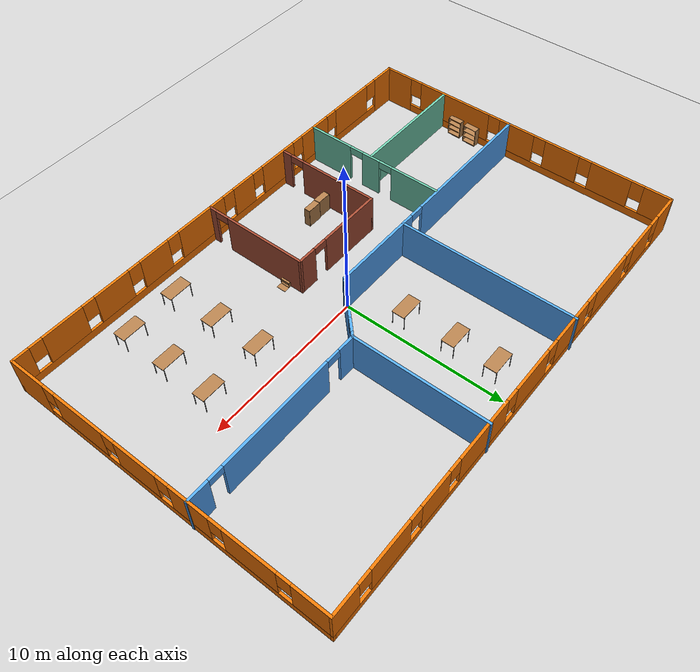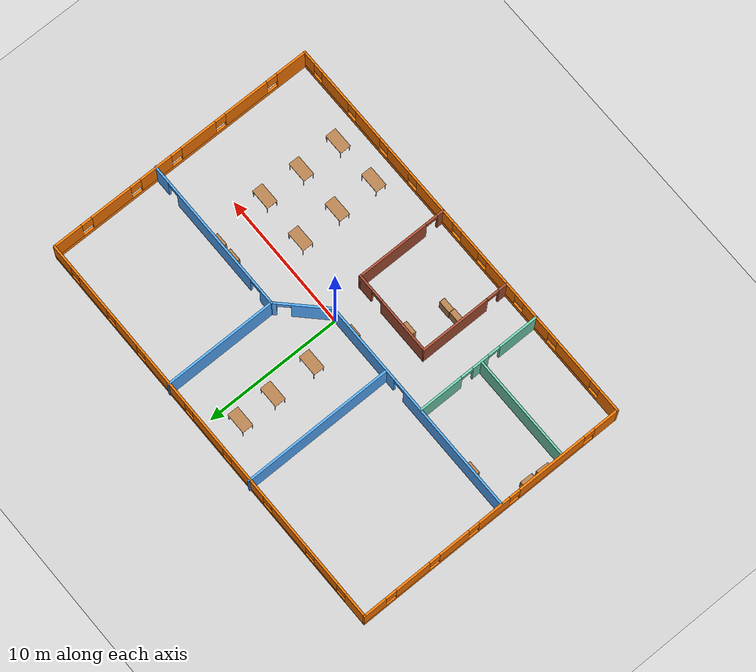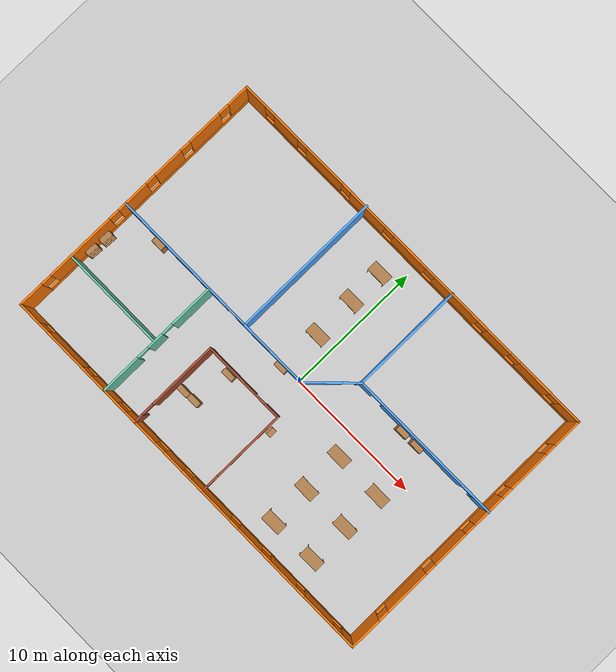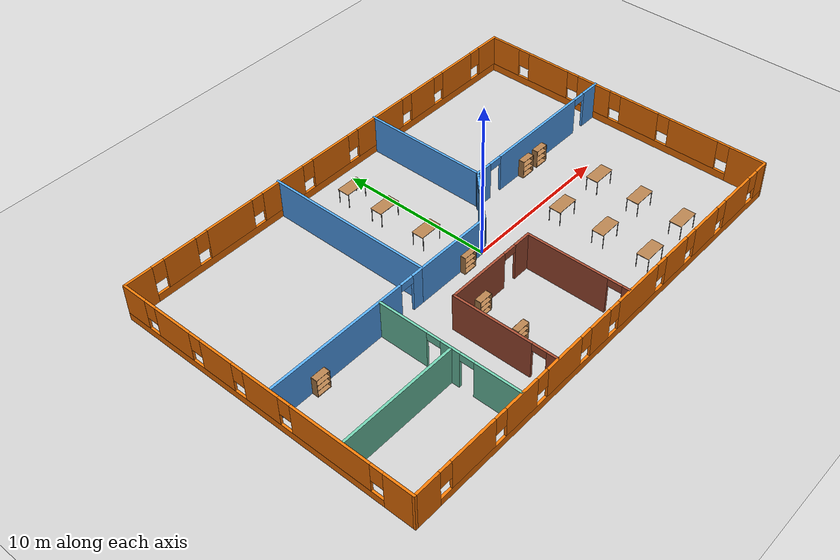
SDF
<sdf version="1.6">
 <world name="default">
  <light name="sun" type="directional">
   <pose>0 0 10 0 -0 0</pose>
   <diffuse>0.8 0.8 0.8 1</diffuse>
   <specular>0.2 0.2 0.2 1</specular>
   <attenuation>
    <range>1000</range>
    <constant>0.9</constant>
    <linear>0.01</linear>
    <quadratic>0.001</quadratic>
   </attenuation>
   <direction>-0.5 0.1 -0.9</direction>
   <spot><inner_angle>0</inner_angle><outer_angle>0</outer_angle><falloff>0</falloff></spot>
  </light>
  <model name="ground_plane">
   <static>1</static>
   <link name="link">
    <collision name="collision">
     <geometry><plane><normal>0 0 1</normal><size>100 100</size></plane></geometry>
     <surface>
      <contact><collide_bitmask>65535</collide_bitmask></contact>
      <friction><ode><mu>100</mu><mu2>50</mu2></ode></friction>
     </surface>
    </collision>
    <visual name="visual">
     <cast_shadows>0</cast_shadows>
     <geometry><plane><normal>0 0 1</normal><size>100 100</size></plane></geometry>
     <material>
      <script><uri>file://media/materials/scripts/gazebo.material</uri><name>Gazebo/Grey</name></script>
     </material>
    </visual>
   </link>
  </model>
  <gravity>0 0 -9.8</gravity>
  <magnetic_field>6e-06 2.3e-05 -4.2e-05</magnetic_field>
  <atmosphere type="adiabatic"/>
  <physics name="default_physics" default="0" type="ode">
   <max_step_size>0.001</max_step_size>
   <real_time_factor>1</real_time_factor>
   <real_time_update_rate>1000</real_time_update_rate>
  </physics>
  <scene><ambient>0.4 0.4 0.4 1</ambient><background>0.7 0.7 0.7 1</background><shadows>1</shadows></scene>
  <spherical_coordinates>
   <surface_model>EARTH_WGS84</surface_model>
   <latitude_deg>0</latitude_deg>
   <longitude_deg>0</longitude_deg>
   <elevation>0</elevation>
   <heading_deg>0</heading_deg>
  </spherical_coordinates>
  <model name="building1">
   <pose>-0.784049 0.80046 0 0 -0 0</pose>
   <link name="Wall_0">
    <pose>-0.018158 -10.0416 0 0 -0 0</pose>
    <visual name="Wall_0_Visual_0">
     <pose>-14.2164 0 1.25 0 -0 0</pose>
     <geometry><box><size>1.7173 0.15 2.5</size></box></geometry>
     <material>
      <script><uri>file://media/materials/scripts/gazebo.material</uri><name>Gazebo/Grey</name></script>
      <ambient>0.996078 0.47451 0.0196078 1</ambient>
     </material>
     <meta><layer>0</layer></meta>
    </visual>
    <collision name="Wall_0_Collision_0">
     <geometry><box><size>1.7173 0.15 2.5</size></box></geometry>
     <pose>-14.2164 0 1.25 0 -0 0</pose>
    </collision>
    <visual name="Wall_0_Visual_1">
     <pose>0.858647 0 0.25 0 -0 0</pose>
     <geometry><box><size>28.4327 0.15 0.5</size></box></geometry>
     <material>
      <script><uri>file://media/materials/scripts/gazebo.material</uri><name>Gazebo/Grey</name></script>
      <ambient>0.996078 0.47451 0.0196078 1</ambient>
     </material>
     <meta><layer>0</layer></meta>
    </visual>
    <collision name="Wall_0_Collision_1">
     <geometry><box><size>28.4327 0.15 0.5</size></box></geometry>
     <pose>0.858647 0 0.25 0 -0 0</pose>
    </collision>
    <visual name="Wall_0_Visual_2">
     <pose>-10.9877 0 1.5 0 -0 0</pose>
     <geometry><box><size>3.14002 0.15 2</size></box></geometry>
     <material>
      <script><uri>file://media/materials/scripts/gazebo.material</uri><name>Gazebo/Grey</name></script>
      <ambient>0.996078 0.47451 0.0196078 1</ambient>
     </material>
     <meta><layer>0</layer></meta>
    </visual>
    <collision name="Wall_0_Collision_2">
     <geometry><box><size>3.14002 0.15 2</size></box></geometry>
     <pose>-10.9877 0 1.5 0 -0 0</pose>
    </collision>
    <visual name="Wall_0_Visual_3">
     <pose>-7.43464 0 1.5 0 -0 0</pose>
     <geometry><box><size>2.36609 0.15 2</size></box></geometry>
     <material>
      <script><uri>file://media/materials/scripts/gazebo.material</uri><name>Gazebo/Grey</name></script>
      <ambient>0.996078 0.47451 0.0196078 1</ambient>
     </material>
     <meta><layer>0</layer></meta>
    </visual>
    <collision name="Wall_0_Collision_3">
     <geometry><box><size>2.36609 0.15 2</size></box></geometry>
     <pose>-7.43464 0 1.5 0 -0 0</pose>
    </collision>
    <visual name="Wall_0_Visual_4">
     <pose>-4.08798 0 1.5 0 -0 0</pose>
     <geometry><box><size>2.72724 0.15 2</size></box></geometry>
     <material>
      <script><uri>file://media/materials/scripts/gazebo.material</uri><name>Gazebo/Grey</name></script>
      <ambient>0.996078 0.47451 0.0196078 1</ambient>
     </material>
     <meta><layer>0</layer></meta>
    </visual>
    <collision name="Wall_0_Collision_4">
     <geometry><box><size>2.72724 0.15 2</size></box></geometry>
     <pose>-4.08798 0 1.5 0 -0 0</pose>
    </collision>
    <visual name="Wall_0_Visual_5">
     <pose>-1.11069 0 1.5 0 -0 0</pose>
     <geometry><box><size>1.62733 0.15 2</size></box></geometry>
     <material>
      <script><uri>file://media/materials/scripts/gazebo.material</uri><name>Gazebo/Grey</name></script>
      <ambient>0.996078 0.47451 0.0196078 1</ambient>
     </material>
     <meta><layer>0</layer></meta>
    </visual>
    <collision name="Wall_0_Collision_5">
     <geometry><box><size>1.62733 0.15 2</size></box></geometry>
     <pose>-1.11069 0 1.5 0 -0 0</pose>
    </collision>
    <visual name="Wall_0_Visual_6">
     <pose>2.2442 0 1.5 0 -0 0</pose>
     <geometry><box><size>3.48244 0.15 2</size></box></geometry>
     <material>
      <script><uri>file://media/materials/scripts/gazebo.material</uri><name>Gazebo/Grey</name></script>
      <ambient>0.996078 0.47451 0.0196078 1</ambient>
     </material>
     <meta><layer>0</layer></meta>
    </visual>
    <collision name="Wall_0_Collision_6">
     <geometry><box><size>3.48244 0.15 2</size></box></geometry>
     <pose>2.2442 0 1.5 0 -0 0</pose>
    </collision>
    <visual name="Wall_0_Visual_7">
     <pose>5.79258 0 1.5 0 -0 0</pose>
     <geometry><box><size>2.0143 0.15 2</size></box></geometry>
     <material>
      <script><uri>file://media/materials/scripts/gazebo.material</uri><name>Gazebo/Grey</name></script>
      <ambient>0.996078 0.47451 0.0196078 1</ambient>
     </material>
     <meta><layer>0</layer></meta>
    </visual>
    <collision name="Wall_0_Collision_7">
     <geometry><box><size>2.0143 0.15 2</size></box></geometry>
     <pose>5.79258 0 1.5 0 -0 0</pose>
    </collision>
    <visual name="Wall_0_Visual_8">
     <pose>8.74759 0 1.5 0 -0 0</pose>
     <geometry><box><size>2.29573 0.15 2</size></box></geometry>
     <material>
      <script><uri>file://media/materials/scripts/gazebo.material</uri><name>Gazebo/Grey</name></script>
      <ambient>0.996078 0.47451 0.0196078 1</ambient>
     </material>
     <meta><layer>0</layer></meta>
    </visual>
    <collision name="Wall_0_Collision_8">
     <geometry><box><size>2.29573 0.15 2</size></box></geometry>
     <pose>8.74759 0 1.5 0 -0 0</pose>
    </collision>
    <visual name="Wall_0_Visual_9">
     <pose>11.9664 0 1.5 0 -0 0</pose>
     <geometry><box><size>2.54198 0.15 2</size></box></geometry>
     <material>
      <script><uri>file://media/materials/scripts/gazebo.material</uri><name>Gazebo/Grey</name></script>
      <ambient>0.996078 0.47451 0.0196078 1</ambient>
     </material>
     <meta><layer>0</layer></meta>
    </visual>
    <collision name="Wall_0_Collision_9">
     <geometry><box><size>2.54198 0.15 2</size></box></geometry>
     <pose>11.9664 0 1.5 0 -0 0</pose>
    </collision>
    <visual name="Wall_0_Visual_10">
     <pose>14.5562 0 1.5 0 -0 0</pose>
     <geometry><box><size>1.03756 0.15 2</size></box></geometry>
     <material>
      <script><uri>file://media/materials/scripts/gazebo.material</uri><name>Gazebo/Grey</name></script>
      <ambient>0.996078 0.47451 0.0196078 1</ambient>
     </material>
     <meta><layer>0</layer></meta>
    </visual>
    <collision name="Wall_0_Collision_10">
     <geometry><box><size>1.03756 0.15 2</size></box></geometry>
     <pose>14.5562 0 1.5 0 -0 0</pose>
    </collision>
    <visual name="Wall_0_Visual_11">
     <pose>-12.9577 0 1.9 0 -0 0</pose>
     <geometry><box><size>0.8 0.15 1.2</size></box></geometry>
     <material>
      <script><uri>file://media/materials/scripts/gazebo.material</uri><name>Gazebo/Grey</name></script>
      <ambient>0.996078 0.47451 0.0196078 1</ambient>
     </material>
     <meta><layer>0</layer></meta>
    </visual>
    <collision name="Wall_0_Collision_11">
     <geometry><box><size>0.8 0.15 1.2</size></box></geometry>
     <pose>-12.9577 0 1.9 0 -0 0</pose>
    </collision>
    <visual name="Wall_0_Visual_12">
     <pose>-9.01768 0 1.9 0 -0 0</pose>
     <geometry><box><size>0.8 0.15 1.2</size></box></geometry>
     <material>
      <script><uri>file://media/materials/scripts/gazebo.material</uri><name>Gazebo/Grey</name></script>
      <ambient>0.996078 0.47451 0.0196078 1</ambient>
     </material>
     <meta><layer>0</layer></meta>
    </visual>
    <collision name="Wall_0_Collision_12">
     <geometry><box><size>0.8 0.15 1.2</size></box></geometry>
     <pose>-9.01768 0 1.9 0 -0 0</pose>
    </collision>
    <visual name="Wall_0_Visual_13">
     <pose>-5.8516 0 1.9 0 -0 0</pose>
     <geometry><box><size>0.8 0.15 1.2</size></box></geometry>
     <material>
      <script><uri>file://media/materials/scripts/gazebo.material</uri><name>Gazebo/Grey</name></script>
      <ambient>0.996078 0.47451 0.0196078 1</ambient>
     </material>
     <meta><layer>0</layer></meta>
    </visual>
    <collision name="Wall_0_Collision_13">
     <geometry><box><size>0.8 0.15 1.2</size></box></geometry>
     <pose>-5.8516 0 1.9 0 -0 0</pose>
    </collision>
    <visual name="Wall_0_Visual_14">
     <pose>-2.32436 0 1.9 0 -0 0</pose>
     <geometry><box><size>0.8 0.15 1.2</size></box></geometry>
     <material>
      <script><uri>file://media/materials/scripts/gazebo.material</uri><name>Gazebo/Grey</name></script>
      <ambient>0.996078 0.47451 0.0196078 1</ambient>
     </material>
     <meta><layer>0</layer></meta>
    </visual>
    <collision name="Wall_0_Collision_14">
     <geometry><box><size>0.8 0.15 1.2</size></box></geometry>
     <pose>-2.32436 0 1.9 0 -0 0</pose>
    </collision>
    <visual name="Wall_0_Visual_15">
     <pose>0.10298 0 1.9 0 -0 0</pose>
     <geometry><box><size>0.8 0.15 1.2</size></box></geometry>
     <material>
      <script><uri>file://media/materials/scripts/gazebo.material</uri><name>Gazebo/Grey</name></script>
      <ambient>0.996078 0.47451 0.0196078 1</ambient>
     </material>
     <meta><layer>0</layer></meta>
    </visual>
    <collision name="Wall_0_Collision_15">
     <geometry><box><size>0.8 0.15 1.2</size></box></geometry>
     <pose>0.10298 0 1.9 0 -0 0</pose>
    </collision>
    <visual name="Wall_0_Visual_16">
     <pose>4.38542 0 1.9 0 -0 0</pose>
     <geometry><box><size>0.8 0.15 1.2</size></box></geometry>
     <material>
      <script><uri>file://media/materials/scripts/gazebo.material</uri><name>Gazebo/Grey</name></script>
      <ambient>0.996078 0.47451 0.0196078 1</ambient>
     </material>
     <meta><layer>0</layer></meta>
    </visual>
    <collision name="Wall_0_Collision_16">
     <geometry><box><size>0.8 0.15 1.2</size></box></geometry>
     <pose>4.38542 0 1.9 0 -0 0</pose>
    </collision>
    <visual name="Wall_0_Visual_17">
     <pose>7.19973 0 1.9 0 -0 0</pose>
     <geometry><box><size>0.8 0.15 1.2</size></box></geometry>
     <material>
      <script><uri>file://media/materials/scripts/gazebo.material</uri><name>Gazebo/Grey</name></script>
      <ambient>0.996078 0.47451 0.0196078 1</ambient>
     </material>
     <meta><layer>0</layer></meta>
    </visual>
    <collision name="Wall_0_Collision_17">
     <geometry><box><size>0.8 0.15 1.2</size></box></geometry>
     <pose>7.19973 0 1.9 0 -0 0</pose>
    </collision>
    <visual name="Wall_0_Visual_18">
     <pose>10.2955 0 1.9 0 -0 0</pose>
     <geometry><box><size>0.8 0.15 1.2</size></box></geometry>
     <material>
      <script><uri>file://media/materials/scripts/gazebo.material</uri><name>Gazebo/Grey</name></script>
      <ambient>0.996078 0.47451 0.0196078 1</ambient>
     </material>
     <meta><layer>0</layer></meta>
    </visual>
    <collision name="Wall_0_Collision_18">
     <geometry><box><size>0.8 0.15 1.2</size></box></geometry>
     <pose>10.2955 0 1.9 0 -0 0</pose>
    </collision>
    <visual name="Wall_0_Visual_19">
     <pose>13.6374 0 1.9 0 -0 0</pose>
     <geometry><box><size>0.8 0.15 1.2</size></box></geometry>
     <material>
      <script><uri>file://media/materials/scripts/gazebo.material</uri><name>Gazebo/Grey</name></script>
      <ambient>0.996078 0.47451 0.0196078 1</ambient>
     </material>
     <meta><layer>0</layer></meta>
    </visual>
    <collision name="Wall_0_Collision_19">
     <geometry><box><size>0.8 0.15 1.2</size></box></geometry>
     <pose>13.6374 0 1.9 0 -0 0</pose>
    </collision>
   </link>
   <link name="Wall_11">
    <pose>-7.3948 -5.44058 0 0 0 -1.5708</pose>
    <visual name="Wall_11_Visual_0">
     <pose>-3.01002 0 1.25 0 -0 0</pose>
     <geometry><box><size>3.22995 0.15 2.5</size></box></geometry>
     <material>
      <script><uri>file://media/materials/scripts/gazebo.material</uri><name>Gazebo/Grey</name></script>
      <ambient>0.435294 0.796078 0.67451 1</ambient>
     </material>
     <meta><layer>0</layer></meta>
    </visual>
    <collision name="Wall_11_Collision_0">
     <geometry><box><size>3.22995 0.15 2.5</size></box></geometry>
     <pose>-3.01002 0 1.25 0 -0 0</pose>
    </collision>
    <visual name="Wall_11_Visual_1">
     <pose>0.127027 0 1.25 0 -0 0</pose>
     <geometry><box><size>1.24415 0.15 2.5</size></box></geometry>
     <material>
      <script><uri>file://media/materials/scripts/gazebo.material</uri><name>Gazebo/Grey</name></script>
      <ambient>0.435294 0.796078 0.67451 1</ambient>
     </material>
     <meta><layer>0</layer></meta>
    </visual>
    <collision name="Wall_11_Collision_1">
     <geometry><box><size>1.24415 0.15 2.5</size></box></geometry>
     <pose>0.127027 0 1.25 0 -0 0</pose>
    </collision>
    <visual name="Wall_11_Visual_2">
     <pose>3.13705 0 1.25 0 -0 0</pose>
     <geometry><box><size>2.9759 0.15 2.5</size></box></geometry>
     <material>
      <script><uri>file://media/materials/scripts/gazebo.material</uri><name>Gazebo/Grey</name></script>
      <ambient>0.435294 0.796078 0.67451 1</ambient>
     </material>
     <meta><layer>0</layer></meta>
    </visual>
    <collision name="Wall_11_Collision_2">
     <geometry><box><size>2.9759 0.15 2.5</size></box></geometry>
     <pose>3.13705 0 1.25 0 -0 0</pose>
    </collision>
    <visual name="Wall_11_Visual_3">
     <pose>-0.945045 0 2.25 0 -0 0</pose>
     <geometry><box><size>0.9 0.15 0.5</size></box></geometry>
     <material>
      <script><uri>file://media/materials/scripts/gazebo.material</uri><name>Gazebo/Grey</name></script>
      <ambient>0.435294 0.796078 0.67451 1</ambient>
     </material>
     <meta><layer>0</layer></meta>
    </visual>
    <collision name="Wall_11_Collision_3">
     <geometry><box><size>0.9 0.15 0.5</size></box></geometry>
     <pose>-0.945045 0 2.25 0 -0 0</pose>
    </collision>
    <visual name="Wall_11_Visual_4">
     <pose>1.1991 0 2.25 0 -0 0</pose>
     <geometry><box><size>0.9 0.15 0.5</size></box></geometry>
     <material>
      <script><uri>file://media/materials/scripts/gazebo.material</uri><name>Gazebo/Grey</name></script>
      <ambient>0.435294 0.796078 0.67451 1</ambient>
     </material>
     <meta><layer>0</layer></meta>
    </visual>
    <collision name="Wall_11_Collision_4">
     <geometry><box><size>0.9 0.15 0.5</size></box></geometry>
     <pose>1.1991 0 2.25 0 -0 0</pose>
    </collision>
   </link>
   <link name="Wall_13">
    <collision name="Wall_13_Collision">
     <geometry><box><size>5.25 0.15 2.5</size></box></geometry>
     <pose>0 0 1.25 0 -0 0</pose>
    </collision>
    <visual name="Wall_13_Visual">
     <pose>0 0 1.25 0 -0 0</pose>
     <geometry><box><size>5.25 0.15 2.5</size></box></geometry>
     <material>
      <script><uri>file://media/materials/scripts/gazebo.material</uri><name>Gazebo/Grey</name></script>
      <ambient>0.333333 0.666667 1 1</ambient>
     </material>
     <meta><layer>0</layer></meta>
    </visual>
    <pose>-1.6042 -0.808364 0 0 -0 0</pose>
   </link>
   <link name="Wall_14">
    <pose>2.30698 0.552817 0 0 -0 0.785398</pose>
    <visual name="Wall_14_Visual_0">
     <pose>-0.648809 0 1.25 0 -0 0</pose>
     <geometry><box><size>2.70238 0.15 2.5</size></box></geometry>
     <material>
      <script><uri>file://media/materials/scripts/gazebo.material</uri><name>Gazebo/Grey</name></script>
      <ambient>0.333333 0.666667 1 1</ambient>
     </material>
     <meta><layer>0</layer></meta>
    </visual>
    <collision name="Wall_14_Collision_0">
     <geometry><box><size>2.70238 0.15 2.5</size></box></geometry>
     <pose>-0.648809 0 1.25 0 -0 0</pose>
    </collision>
    <visual name="Wall_14_Visual_1">
     <pose>1.80119 0 1.25 0 -0 0</pose>
     <geometry><box><size>0.397618 0.15 2.5</size></box></geometry>
     <material>
      <script><uri>file://media/materials/scripts/gazebo.material</uri><name>Gazebo/Grey</name></script>
      <ambient>0.333333 0.666667 1 1</ambient>
     </material>
     <meta><layer>0</layer></meta>
    </visual>
    <collision name="Wall_14_Collision_1">
     <geometry><box><size>0.397618 0.15 2.5</size></box></geometry>
     <pose>1.80119 0 1.25 0 -0 0</pose>
    </collision>
    <visual name="Wall_14_Visual_2">
     <pose>1.15238 0 2.25 0 -0 0</pose>
     <geometry><box><size>0.9 0.15 0.5</size></box></geometry>
     <material>
      <script><uri>file://media/materials/scripts/gazebo.material</uri><name>Gazebo/Grey</name></script>
      <ambient>0.333333 0.666667 1 1</ambient>
     </material>
     <meta><layer>0</layer></meta>
    </visual>
    <collision name="Wall_14_Collision_2">
     <geometry><box><size>0.9 0.15 0.5</size></box></geometry>
     <pose>1.15238 0 2.25 0 -0 0</pose>
    </collision>
   </link>
   <link name="Wall_15">
    <collision name="Wall_15_Collision">
     <geometry><box><size>8.25 0.15 2.5</size></box></geometry>
     <pose>0 0 1.25 0 -0 0</pose>
    </collision>
    <visual name="Wall_15_Visual">
     <pose>0 0 1.25 0 -0 0</pose>
     <geometry><box><size>8.25 0.15 2.5</size></box></geometry>
     <material>
      <script><uri>file://media/materials/scripts/gazebo.material</uri><name>Gazebo/Grey</name></script>
      <ambient>0.333333 0.666667 1 1</ambient>
     </material>
     <meta><layer>0</layer></meta>
    </visual>
    <pose>3.66816 5.964 0 0 -0 1.5708</pose>
   </link>
   <link name="Wall_17">
    <pose>9.34316 1.914 0 0 -0 0</pose>
    <visual name="Wall_17_Visual_0">
     <pose>-5.18047 0 1.25 0 -0 0</pose>
     <geometry><box><size>1.13906 0.15 2.5</size></box></geometry>
     <material>
      <script><uri>file://media/materials/scripts/gazebo.material</uri><name>Gazebo/Grey</name></script>
      <ambient>0.333333 0.666667 1 1</ambient>
     </material>
     <meta><layer>0</layer></meta>
    </visual>
    <collision name="Wall_17_Collision_0">
     <geometry><box><size>1.13906 0.15 2.5</size></box></geometry>
     <pose>-5.18047 0 1.25 0 -0 0</pose>
    </collision>
    <visual name="Wall_17_Visual_1">
     <pose>-0.115377 0 1.25 0 -0 0</pose>
     <geometry><box><size>7.19111 0.15 2.5</size></box></geometry>
     <material>
      <script><uri>file://media/materials/scripts/gazebo.material</uri><name>Gazebo/Grey</name></script>
      <ambient>0.333333 0.666667 1 1</ambient>
     </material>
     <meta><layer>0</layer></meta>
    </visual>
    <collision name="Wall_17_Collision_1">
     <geometry><box><size>7.19111 0.15 2.5</size></box></geometry>
     <pose>-0.115377 0 1.25 0 -0 0</pose>
    </collision>
    <visual name="Wall_17_Visual_2">
     <pose>5.06509 0 1.25 0 -0 0</pose>
     <geometry><box><size>1.36982 0.15 2.5</size></box></geometry>
     <material>
      <script><uri>file://media/materials/scripts/gazebo.material</uri><name>Gazebo/Grey</name></script>
      <ambient>0.333333 0.666667 1 1</ambient>
     </material>
     <meta><layer>0</layer></meta>
    </visual>
    <collision name="Wall_17_Collision_2">
     <geometry><box><size>1.36982 0.15 2.5</size></box></geometry>
     <pose>5.06509 0 1.25 0 -0 0</pose>
    </collision>
    <visual name="Wall_17_Visual_3">
     <pose>-4.16094 0 2.25 0 -0 0</pose>
     <geometry><box><size>0.9 0.15 0.5</size></box></geometry>
     <material>
      <script><uri>file://media/materials/scripts/gazebo.material</uri><name>Gazebo/Grey</name></script>
      <ambient>0.333333 0.666667 1 1</ambient>
     </material>
     <meta><layer>0</layer></meta>
    </visual>
    <collision name="Wall_17_Collision_3">
     <geometry><box><size>0.9 0.15 0.5</size></box></geometry>
     <pose>-4.16094 0 2.25 0 -0 0</pose>
    </collision>
    <visual name="Wall_17_Visual_4">
     <pose>3.93018 0 2.25 0 -0 0</pose>
     <geometry><box><size>0.9 0.15 0.5</size></box></geometry>
     <material>
      <script><uri>file://media/materials/scripts/gazebo.material</uri><name>Gazebo/Grey</name></script>
      <ambient>0.333333 0.666667 1 1</ambient>
     </material>
     <meta><layer>0</layer></meta>
    </visual>
    <collision name="Wall_17_Collision_4">
     <geometry><box><size>0.9 0.15 0.5</size></box></geometry>
     <pose>3.93018 0 2.25 0 -0 0</pose>
    </collision>
   </link>
   <link name="Wall_19">
    <collision name="Wall_19_Collision">
     <geometry><box><size>7.5 0.15 2.5</size></box></geometry>
     <pose>0 0 1.25 0 -0 0</pose>
    </collision>
    <visual name="Wall_19_Visual">
     <pose>0 0 1.25 0 -0 0</pose>
     <geometry><box><size>7.5 0.15 2.5</size></box></geometry>
     <material>
      <script><uri>file://media/materials/scripts/gazebo.material</uri><name>Gazebo/Grey</name></script>
      <ambient>0.435294 0.796078 0.67451 1</ambient>
     </material>
     <meta><layer>0</layer></meta>
    </visual>
    <pose>-11.1958 -5.62829 0 0 -0 3.14159</pose>
   </link>
   <link name="Wall_2">
    <pose>-15.0182 -0.041636 0 0 -0 1.5708</pose>
    <visual name="Wall_2_Visual_0">
     <pose>-9.11261 0 1.25 0 -0 0</pose>
     <geometry><box><size>1.92478 0.15 2.5</size></box></geometry>
     <material>
      <script><uri>file://media/materials/scripts/gazebo.material</uri><name>Gazebo/Grey</name></script>
      <ambient>0.996078 0.47451 0.0196078 1</ambient>
     </material>
     <meta><layer>0</layer></meta>
    </visual>
    <collision name="Wall_2_Collision_0">
     <geometry><box><size>1.92478 0.15 2.5</size></box></geometry>
     <pose>-9.11261 0 1.25 0 -0 0</pose>
    </collision>
    <visual name="Wall_2_Visual_1">
     <pose>0.962392 0 0.25 0 -0 0</pose>
     <geometry><box><size>18.2252 0.15 0.5</size></box></geometry>
     <material>
      <script><uri>file://media/materials/scripts/gazebo.material</uri><name>Gazebo/Grey</name></script>
      <ambient>0.996078 0.47451 0.0196078 1</ambient>
     </material>
     <meta><layer>0</layer></meta>
    </visual>
    <collision name="Wall_2_Collision_1">
     <geometry><box><size>18.2252 0.15 0.5</size></box></geometry>
     <pose>0.962392 0 0.25 0 -0 0</pose>
    </collision>
    <visual name="Wall_2_Visual_2">
     <pose>-4.77761 0 1.5 0 -0 0</pose>
     <geometry><box><size>5.14521 0.15 2</size></box></geometry>
     <material>
      <script><uri>file://media/materials/scripts/gazebo.material</uri><name>Gazebo/Grey</name></script>
      <ambient>0.996078 0.47451 0.0196078 1</ambient>
     </material>
     <meta><layer>0</layer></meta>
    </visual>
    <collision name="Wall_2_Collision_2">
     <geometry><box><size>5.14521 0.15 2</size></box></geometry>
     <pose>-4.77761 0 1.5 0 -0 0</pose>
    </collision>
    <visual name="Wall_2_Visual_3">
     <pose>-0.186783 0 1.5 0 -0 0</pose>
     <geometry><box><size>2.43645 0.15 2</size></box></geometry>
     <material>
      <script><uri>file://media/materials/scripts/gazebo.material</uri><name>Gazebo/Grey</name></script>
      <ambient>0.996078 0.47451 0.0196078 1</ambient>
     </material>
     <meta><layer>0</layer></meta>
    </visual>
    <collision name="Wall_2_Collision_3">
     <geometry><box><size>2.43645 0.15 2</size></box></geometry>
     <pose>-0.186783 0 1.5 0 -0 0</pose>
    </collision>
    <visual name="Wall_2_Visual_4">
     <pose>2.97931 0 1.5 0 -0 0</pose>
     <geometry><box><size>2.29573 0.15 2</size></box></geometry>
     <material>
      <script><uri>file://media/materials/scripts/gazebo.material</uri><name>Gazebo/Grey</name></script>
      <ambient>0.996078 0.47451 0.0196078 1</ambient>
     </material>
     <meta><layer>0</layer></meta>
    </visual>
    <collision name="Wall_2_Collision_4">
     <geometry><box><size>2.29573 0.15 2</size></box></geometry>
     <pose>2.97931 0 1.5 0 -0 0</pose>
    </collision>
    <visual name="Wall_2_Visual_5">
     <pose>6.23334 0 1.5 0 -0 0</pose>
     <geometry><box><size>2.61234 0.15 2</size></box></geometry>
     <material>
      <script><uri>file://media/materials/scripts/gazebo.material</uri><name>Gazebo/Grey</name></script>
      <ambient>0.996078 0.47451 0.0196078 1</ambient>
     </material>
     <meta><layer>0</layer></meta>
    </visual>
    <collision name="Wall_2_Collision_5">
     <geometry><box><size>2.61234 0.15 2</size></box></geometry>
     <pose>6.23334 0 1.5 0 -0 0</pose>
    </collision>
    <visual name="Wall_2_Visual_6">
     <pose>9.20726 0 1.5 0 -0 0</pose>
     <geometry><box><size>1.73549 0.15 2</size></box></geometry>
     <material>
      <script><uri>file://media/materials/scripts/gazebo.material</uri><name>Gazebo/Grey</name></script>
      <ambient>0.996078 0.47451 0.0196078 1</ambient>
     </material>
     <meta><layer>0</layer></meta>
    </visual>
    <collision name="Wall_2_Collision_6">
     <geometry><box><size>1.73549 0.15 2</size></box></geometry>
     <pose>9.20726 0 1.5 0 -0 0</pose>
    </collision>
    <visual name="Wall_2_Visual_7">
     <pose>-7.75022 0 1.9 0 -0 0</pose>
     <geometry><box><size>0.8 0.15 1.2</size></box></geometry>
     <material>
      <script><uri>file://media/materials/scripts/gazebo.material</uri><name>Gazebo/Grey</name></script>
      <ambient>0.996078 0.47451 0.0196078 1</ambient>
     </material>
     <meta><layer>0</layer></meta>
    </visual>
    <collision name="Wall_2_Collision_7">
     <geometry><box><size>0.8 0.15 1.2</size></box></geometry>
     <pose>-7.75022 0 1.9 0 -0 0</pose>
    </collision>
    <visual name="Wall_2_Visual_8">
     <pose>-1.80501 0 1.9 0 -0 0</pose>
     <geometry><box><size>0.8 0.15 1.2</size></box></geometry>
     <material>
      <script><uri>file://media/materials/scripts/gazebo.material</uri><name>Gazebo/Grey</name></script>
      <ambient>0.996078 0.47451 0.0196078 1</ambient>
     </material>
     <meta><layer>0</layer></meta>
    </visual>
    <collision name="Wall_2_Collision_8">
     <geometry><box><size>0.8 0.15 1.2</size></box></geometry>
     <pose>-1.80501 0 1.9 0 -0 0</pose>
    </collision>
    <visual name="Wall_2_Visual_9">
     <pose>1.43144 0 1.9 0 -0 0</pose>
     <geometry><box><size>0.8 0.15 1.2</size></box></geometry>
     <material>
      <script><uri>file://media/materials/scripts/gazebo.material</uri><name>Gazebo/Grey</name></script>
      <ambient>0.996078 0.47451 0.0196078 1</ambient>
     </material>
     <meta><layer>0</layer></meta>
    </visual>
    <collision name="Wall_2_Collision_9">
     <geometry><box><size>0.8 0.15 1.2</size></box></geometry>
     <pose>1.43144 0 1.9 0 -0 0</pose>
    </collision>
    <visual name="Wall_2_Visual_10">
     <pose>4.52717 0 1.9 0 -0 0</pose>
     <geometry><box><size>0.8 0.15 1.2</size></box></geometry>
     <material>
      <script><uri>file://media/materials/scripts/gazebo.material</uri><name>Gazebo/Grey</name></script>
      <ambient>0.996078 0.47451 0.0196078 1</ambient>
     </material>
     <meta><layer>0</layer></meta>
    </visual>
    <collision name="Wall_2_Collision_10">
     <geometry><box><size>0.8 0.15 1.2</size></box></geometry>
     <pose>4.52717 0 1.9 0 -0 0</pose>
    </collision>
    <visual name="Wall_2_Visual_11">
     <pose>7.93951 0 1.9 0 -0 0</pose>
     <geometry><box><size>0.8 0.15 1.2</size></box></geometry>
     <material>
      <script><uri>file://media/materials/scripts/gazebo.material</uri><name>Gazebo/Grey</name></script>
      <ambient>0.996078 0.47451 0.0196078 1</ambient>
     </material>
     <meta><layer>0</layer></meta>
    </visual>
    <collision name="Wall_2_Collision_11">
     <geometry><box><size>0.8 0.15 1.2</size></box></geometry>
     <pose>7.93951 0 1.9 0 -0 0</pose>
    </collision>
   </link>
   <link name="Wall_23">
    <pose>-4.60803 -6.6975 0 0 -0 1.5708</pose>
    <visual name="Wall_23_Visual_0">
     <pose>-3.01635 0 1.25 0 -0 0</pose>
     <geometry><box><size>0.717301 0.15 2.5</size></box></geometry>
     <material>
      <script><uri>file://media/materials/scripts/gazebo.material</uri><name>Gazebo/Bricks</name></script>
      <ambient>0.435294 0.796078 0.67451 1</ambient>
     </material>
     <meta><layer>0</layer></meta>
    </visual>
    <collision name="Wall_23_Collision_0">
     <geometry><box><size>0.717301 0.15 2.5</size></box></geometry>
     <pose>-3.01635 0 1.25 0 -0 0</pose>
    </collision>
    <visual name="Wall_23_Visual_1">
     <pose>0.80865 0 1.25 0 -0 0</pose>
     <geometry><box><size>5.1327 0.15 2.5</size></box></geometry>
     <material>
      <script><uri>file://media/materials/scripts/gazebo.material</uri><name>Gazebo/Bricks</name></script>
      <ambient>0.435294 0.796078 0.67451 1</ambient>
     </material>
     <meta><layer>0</layer></meta>
    </visual>
    <collision name="Wall_23_Collision_1">
     <geometry><box><size>5.1327 0.15 2.5</size></box></geometry>
     <pose>0.80865 0 1.25 0 -0 0</pose>
    </collision>
    <visual name="Wall_23_Visual_2">
     <pose>-2.2077 0 2.25 0 -0 0</pose>
     <geometry><box><size>0.9 0.15 0.5</size></box></geometry>
     <material>
      <script><uri>file://media/materials/scripts/gazebo.material</uri><name>Gazebo/Bricks</name></script>
      <ambient>0.435294 0.796078 0.67451 1</ambient>
     </material>
     <meta><layer>0</layer></meta>
    </visual>
    <collision name="Wall_23_Collision_2">
     <geometry><box><size>0.9 0.15 0.5</size></box></geometry>
     <pose>-2.2077 0 2.25 0 -0 0</pose>
    </collision>
   </link>
   <link name="Wall_24">
    <pose>-1.55802 -3.3975 0 0 -0 0</pose>
    <visual name="Wall_24_Visual_0">
     <pose>-1.06722 0 1.25 0 -0 0</pose>
     <geometry><box><size>4.11557 0.15 2.5</size></box></geometry>
     <material>
      <script><uri>file://media/materials/scripts/gazebo.material</uri><name>Gazebo/Bricks</name></script>
      <ambient>0.435294 0.796078 0.67451 1</ambient>
     </material>
     <meta><layer>0</layer></meta>
    </visual>
    <collision name="Wall_24_Collision_0">
     <geometry><box><size>4.11557 0.15 2.5</size></box></geometry>
     <pose>-1.06722 0 1.25 0 -0 0</pose>
    </collision>
    <visual name="Wall_24_Visual_1">
     <pose>2.50779 0 1.25 0 -0 0</pose>
     <geometry><box><size>1.23443 0.15 2.5</size></box></geometry>
     <material>
      <script><uri>file://media/materials/scripts/gazebo.material</uri><name>Gazebo/Bricks</name></script>
      <ambient>0.435294 0.796078 0.67451 1</ambient>
     </material>
     <meta><layer>0</layer></meta>
    </visual>
    <collision name="Wall_24_Collision_1">
     <geometry><box><size>1.23443 0.15 2.5</size></box></geometry>
     <pose>2.50779 0 1.25 0 -0 0</pose>
    </collision>
    <visual name="Wall_24_Visual_2">
     <pose>1.44057 0 2.25 0 -0 0</pose>
     <geometry><box><size>0.9 0.15 0.5</size></box></geometry>
     <material>
      <script><uri>file://media/materials/scripts/gazebo.material</uri><name>Gazebo/Bricks</name></script>
      <ambient>0.435294 0.796078 0.67451 1</ambient>
     </material>
     <meta><layer>0</layer></meta>
    </visual>
    <collision name="Wall_24_Collision_2">
     <geometry><box><size>0.9 0.15 0.5</size></box></geometry>
     <pose>1.44057 0 2.25 0 -0 0</pose>
    </collision>
   </link>
   <link name="Wall_25">
    <pose>1.49197 -6.6975 0 0 0 -1.5708</pose>
    <visual name="Wall_25_Visual_0">
     <pose>-0.707511 0 1.25 0 -0 0</pose>
     <geometry><box><size>5.33498 0.15 2.5</size></box></geometry>
     <material>
      <script><uri>file://media/materials/scripts/gazebo.material</uri><name>Gazebo/Bricks</name></script>
      <ambient>0.435294 0.796078 0.67451 1</ambient>
     </material>
     <meta><layer>0</layer></meta>
    </visual>
    <collision name="Wall_25_Collision_0">
     <geometry><box><size>5.33498 0.15 2.5</size></box></geometry>
     <pose>-0.707511 0 1.25 0 -0 0</pose>
    </collision>
    <visual name="Wall_25_Visual_1">
     <pose>3.11749 0 1.25 0 -0 0</pose>
     <geometry><box><size>0.515023 0.15 2.5</size></box></geometry>
     <material>
      <script><uri>file://media/materials/scripts/gazebo.material</uri><name>Gazebo/Bricks</name></script>
      <ambient>0.435294 0.796078 0.67451 1</ambient>
     </material>
     <meta><layer>0</layer></meta>
    </visual>
    <collision name="Wall_25_Collision_1">
     <geometry><box><size>0.515023 0.15 2.5</size></box></geometry>
     <pose>3.11749 0 1.25 0 -0 0</pose>
    </collision>
    <visual name="Wall_25_Visual_2">
     <pose>2.40998 0 2.25 0 -0 0</pose>
     <geometry><box><size>0.9 0.15 0.5</size></box></geometry>
     <material>
      <script><uri>file://media/materials/scripts/gazebo.material</uri><name>Gazebo/Bricks</name></script>
      <ambient>0.435294 0.796078 0.67451 1</ambient>
     </material>
     <meta><layer>0</layer></meta>
    </visual>
    <collision name="Wall_25_Collision_2">
     <geometry><box><size>0.9 0.15 0.5</size></box></geometry>
     <pose>2.40998 0 2.25 0 -0 0</pose>
    </collision>
   </link>
   <link name="Wall_4">
    <pose>-0.018158 9.95836 0 0 -0 0</pose>
    <visual name="Wall_4_Visual_0">
     <pose>-14.1636 0 1.25 0 -0 0</pose>
     <geometry><box><size>1.82283 0.15 2.5</size></box></geometry>
     <material>
      <script><uri>file://media/materials/scripts/gazebo.material</uri><name>Gazebo/Grey</name></script>
      <ambient>0.996078 0.47451 0.0196078 1</ambient>
     </material>
     <meta><layer>0</layer></meta>
    </visual>
    <collision name="Wall_4_Collision_0">
     <geometry><box><size>1.82283 0.15 2.5</size></box></geometry>
     <pose>-14.1636 0 1.25 0 -0 0</pose>
    </collision>
    <visual name="Wall_4_Visual_1">
     <pose>0.911415 0 0.25 0 -0 0</pose>
     <geometry><box><size>28.3272 0.15 0.5</size></box></geometry>
     <material>
      <script><uri>file://media/materials/scripts/gazebo.material</uri><name>Gazebo/Grey</name></script>
      <ambient>0.996078 0.47451 0.0196078 1</ambient>
     </material>
     <meta><layer>0</layer></meta>
    </visual>
    <collision name="Wall_4_Collision_1">
     <geometry><box><size>28.3272 0.15 0.5</size></box></geometry>
     <pose>0.911415 0 0.25 0 -0 0</pose>
    </collision>
    <visual name="Wall_4_Visual_2">
     <pose>-11.3747 0 1.5 0 -0 0</pose>
     <geometry><box><size>2.15502 0.15 2</size></box></geometry>
     <material>
      <script><uri>file://media/materials/scripts/gazebo.material</uri><name>Gazebo/Grey</name></script>
      <ambient>0.996078 0.47451 0.0196078 1</ambient>
     </material>
     <meta><layer>0</layer></meta>
    </visual>
    <collision name="Wall_4_Collision_2">
     <geometry><box><size>2.15502 0.15 2</size></box></geometry>
     <pose>-11.3747 0 1.5 0 -0 0</pose>
    </collision>
    <visual name="Wall_4_Visual_3">
     <pose>-7.87437 0 1.5 0 -0 0</pose>
     <geometry><box><size>3.24556 0.15 2</size></box></geometry>
     <material>
      <script><uri>file://media/materials/scripts/gazebo.material</uri><name>Gazebo/Grey</name></script>
      <ambient>0.996078 0.47451 0.0196078 1</ambient>
     </material>
     <meta><layer>0</layer></meta>
    </visual>
    <collision name="Wall_4_Collision_3">
     <geometry><box><size>3.24556 0.15 2</size></box></geometry>
     <pose>-7.87437 0 1.5 0 -0 0</pose>
    </collision>
    <visual name="Wall_4_Visual_4">
     <pose>-3.89917 0 1.5 0 -0 0</pose>
     <geometry><box><size>3.10484 0.15 2</size></box></geometry>
     <material>
      <script><uri>file://media/materials/scripts/gazebo.material</uri><name>Gazebo/Grey</name></script>
      <ambient>0.996078 0.47451 0.0196078 1</ambient>
     </material>
     <meta><layer>0</layer></meta>
    </visual>
    <collision name="Wall_4_Collision_4">
     <geometry><box><size>3.10484 0.15 2</size></box></geometry>
     <pose>-3.89917 0 1.5 0 -0 0</pose>
    </collision>
    <visual name="Wall_4_Visual_5">
     <pose>-0.099868 0 1.5 0 -0 0</pose>
     <geometry><box><size>2.89377 0.15 2</size></box></geometry>
     <material>
      <script><uri>file://media/materials/scripts/gazebo.material</uri><name>Gazebo/Grey</name></script>
      <ambient>0.996078 0.47451 0.0196078 1</ambient>
     </material>
     <meta><layer>0</layer></meta>
    </visual>
    <collision name="Wall_4_Collision_5">
     <geometry><box><size>2.89377 0.15 2</size></box></geometry>
     <pose>-0.099868 0 1.5 0 -0 0</pose>
    </collision>
    <visual name="Wall_4_Visual_6">
     <pose>4.10399 0 1.5 0 -0 0</pose>
     <geometry><box><size>3.91395 0.15 2</size></box></geometry>
     <material>
      <script><uri>file://media/materials/scripts/gazebo.material</uri><name>Gazebo/Grey</name></script>
      <ambient>0.996078 0.47451 0.0196078 1</ambient>
     </material>
     <meta><layer>0</layer></meta>
    </visual>
    <collision name="Wall_4_Collision_6">
     <geometry><box><size>3.91395 0.15 2</size></box></geometry>
     <pose>4.10399 0 1.5 0 -0 0</pose>
    </collision>
    <visual name="Wall_4_Visual_7">
     <pose>7.92089 0 1.5 0 -0 0</pose>
     <geometry><box><size>2.11984 0.15 2</size></box></geometry>
     <material>
      <script><uri>file://media/materials/scripts/gazebo.material</uri><name>Gazebo/Grey</name></script>
      <ambient>0.996078 0.47451 0.0196078 1</ambient>
     </material>
     <meta><layer>0</layer></meta>
    </visual>
    <collision name="Wall_4_Collision_7">
     <geometry><box><size>2.11984 0.15 2</size></box></geometry>
     <pose>7.92089 0 1.5 0 -0 0</pose>
    </collision>
    <visual name="Wall_4_Visual_8">
     <pose>11.1573 0 1.5 0 -0 0</pose>
     <geometry><box><size>2.75305 0.15 2</size></box></geometry>
     <material>
      <script><uri>file://media/materials/scripts/gazebo.material</uri><name>Gazebo/Grey</name></script>
      <ambient>0.996078 0.47451 0.0196078 1</ambient>
     </material>
     <meta><layer>0</layer></meta>
    </visual>
    <collision name="Wall_4_Collision_8">
     <geometry><box><size>2.75305 0.15 2</size></box></geometry>
     <pose>11.1573 0 1.5 0 -0 0</pose>
    </collision>
    <visual name="Wall_4_Visual_9">
     <pose>14.2044 0 1.5 0 -0 0</pose>
     <geometry><box><size>1.74114 0.15 2</size></box></geometry>
     <material>
      <script><uri>file://media/materials/scripts/gazebo.material</uri><name>Gazebo/Grey</name></script>
      <ambient>0.996078 0.47451 0.0196078 1</ambient>
     </material>
     <meta><layer>0</layer></meta>
    </visual>
    <collision name="Wall_4_Collision_9">
     <geometry><box><size>1.74114 0.15 2</size></box></geometry>
     <pose>14.2044 0 1.5 0 -0 0</pose>
    </collision>
    <visual name="Wall_4_Visual_10">
     <pose>-12.8522 0 1.9 0 -0 0</pose>
     <geometry><box><size>0.8 0.15 1.2</size></box></geometry>
     <material>
      <script><uri>file://media/materials/scripts/gazebo.material</uri><name>Gazebo/Grey</name></script>
      <ambient>0.996078 0.47451 0.0196078 1</ambient>
     </material>
     <meta><layer>0</layer></meta>
    </visual>
    <collision name="Wall_4_Collision_10">
     <geometry><box><size>0.8 0.15 1.2</size></box></geometry>
     <pose>-12.8522 0 1.9 0 -0 0</pose>
    </collision>
    <visual name="Wall_4_Visual_11">
     <pose>-9.89715 0 1.9 0 -0 0</pose>
     <geometry><box><size>0.8 0.15 1.2</size></box></geometry>
     <material>
      <script><uri>file://media/materials/scripts/gazebo.material</uri><name>Gazebo/Grey</name></script>
      <ambient>0.996078 0.47451 0.0196078 1</ambient>
     </material>
     <meta><layer>0</layer></meta>
    </visual>
    <collision name="Wall_4_Collision_11">
     <geometry><box><size>0.8 0.15 1.2</size></box></geometry>
     <pose>-9.89715 0 1.9 0 -0 0</pose>
    </collision>
    <visual name="Wall_4_Visual_12">
     <pose>-5.8516 0 1.9 0 -0 0</pose>
     <geometry><box><size>0.8 0.15 1.2</size></box></geometry>
     <material>
      <script><uri>file://media/materials/scripts/gazebo.material</uri><name>Gazebo/Grey</name></script>
      <ambient>0.996078 0.47451 0.0196078 1</ambient>
     </material>
     <meta><layer>0</layer></meta>
    </visual>
    <collision name="Wall_4_Collision_12">
     <geometry><box><size>0.8 0.15 1.2</size></box></geometry>
     <pose>-5.8516 0 1.9 0 -0 0</pose>
    </collision>
    <visual name="Wall_4_Visual_13">
     <pose>-1.94675 0 1.9 0 -0 0</pose>
     <geometry><box><size>0.8 0.15 1.2</size></box></geometry>
     <material>
      <script><uri>file://media/materials/scripts/gazebo.material</uri><name>Gazebo/Grey</name></script>
      <ambient>0.996078 0.47451 0.0196078 1</ambient>
     </material>
     <meta><layer>0</layer></meta>
    </visual>
    <collision name="Wall_4_Collision_13">
     <geometry><box><size>0.8 0.15 1.2</size></box></geometry>
     <pose>-1.94675 0 1.9 0 -0 0</pose>
    </collision>
    <visual name="Wall_4_Visual_14">
     <pose>1.74702 0 1.9 0 -0 0</pose>
     <geometry><box><size>0.8 0.15 1.2</size></box></geometry>
     <material>
      <script><uri>file://media/materials/scripts/gazebo.material</uri><name>Gazebo/Grey</name></script>
      <ambient>0.996078 0.47451 0.0196078 1</ambient>
     </material>
     <meta><layer>0</layer></meta>
    </visual>
    <collision name="Wall_4_Collision_14">
     <geometry><box><size>0.8 0.15 1.2</size></box></geometry>
     <pose>1.74702 0 1.9 0 -0 0</pose>
    </collision>
    <visual name="Wall_4_Visual_15">
     <pose>6.46097 0 1.9 0 -0 0</pose>
     <geometry><box><size>0.8 0.15 1.2</size></box></geometry>
     <material>
      <script><uri>file://media/materials/scripts/gazebo.material</uri><name>Gazebo/Grey</name></script>
      <ambient>0.996078 0.47451 0.0196078 1</ambient>
     </material>
     <meta><layer>0</layer></meta>
    </visual>
    <collision name="Wall_4_Collision_15">
     <geometry><box><size>0.8 0.15 1.2</size></box></geometry>
     <pose>6.46097 0 1.9 0 -0 0</pose>
    </collision>
    <visual name="Wall_4_Visual_16">
     <pose>9.38081 0 1.9 0 -0 0</pose>
     <geometry><box><size>0.8 0.15 1.2</size></box></geometry>
     <material>
      <script><uri>file://media/materials/scripts/gazebo.material</uri><name>Gazebo/Grey</name></script>
      <ambient>0.996078 0.47451 0.0196078 1</ambient>
     </material>
     <meta><layer>0</layer></meta>
    </visual>
    <collision name="Wall_4_Collision_16">
     <geometry><box><size>0.8 0.15 1.2</size></box></geometry>
     <pose>9.38081 0 1.9 0 -0 0</pose>
    </collision>
    <visual name="Wall_4_Visual_17">
     <pose>12.9339 0 1.9 0 -0 0</pose>
     <geometry><box><size>0.8 0.15 1.2</size></box></geometry>
     <material>
      <script><uri>file://media/materials/scripts/gazebo.material</uri><name>Gazebo/Grey</name></script>
      <ambient>0.996078 0.47451 0.0196078 1</ambient>
     </material>
     <meta><layer>0</layer></meta>
    </visual>
    <collision name="Wall_4_Collision_17">
     <geometry><box><size>0.8 0.15 1.2</size></box></geometry>
     <pose>12.9339 0 1.9 0 -0 0</pose>
    </collision>
   </link>
   <link name="Wall_6">
    <pose>14.9818 -0.041636 0 0 -0 1.5708</pose>
    <visual name="Wall_6_Visual_0">
     <pose>-8.88395 0 1.25 0 -0 0</pose>
     <geometry><box><size>2.38211 0.15 2.5</size></box></geometry>
     <material>
      <script><uri>file://media/materials/scripts/gazebo.material</uri><name>Gazebo/Grey</name></script>
      <ambient>0.996078 0.47451 0.0196078 1</ambient>
     </material>
     <meta><layer>0</layer></meta>
    </visual>
    <collision name="Wall_6_Collision_0">
     <geometry><box><size>2.38211 0.15 2.5</size></box></geometry>
     <pose>-8.88395 0 1.25 0 -0 0</pose>
    </collision>
    <visual name="Wall_6_Visual_1">
     <pose>1.19105 0 0.25 0 -0 0</pose>
     <geometry><box><size>17.7679 0.15 0.5</size></box></geometry>
     <material>
      <script><uri>file://media/materials/scripts/gazebo.material</uri><name>Gazebo/Grey</name></script>
      <ambient>0.996078 0.47451 0.0196078 1</ambient>
     </material>
     <meta><layer>0</layer></meta>
    </visual>
    <collision name="Wall_6_Collision_1">
     <geometry><box><size>17.7679 0.15 0.5</size></box></geometry>
     <pose>1.19105 0 0.25 0 -0 0</pose>
    </collision>
    <visual name="Wall_6_Visual_2">
     <pose>-5.21735 0 1.5 0 -0 0</pose>
     <geometry><box><size>3.35109 0.15 2</size></box></geometry>
     <material>
      <script><uri>file://media/materials/scripts/gazebo.material</uri><name>Gazebo/Grey</name></script>
      <ambient>0.996078 0.47451 0.0196078 1</ambient>
     </material>
     <meta><layer>0</layer></meta>
    </visual>
    <collision name="Wall_6_Collision_2">
     <geometry><box><size>3.35109 0.15 2</size></box></geometry>
     <pose>-5.21735 0 1.5 0 -0 0</pose>
    </collision>
    <visual name="Wall_6_Visual_3">
     <pose>-1.38286 0 1.5 0 -0 0</pose>
     <geometry><box><size>2.71788 0.15 2</size></box></geometry>
     <material>
      <script><uri>file://media/materials/scripts/gazebo.material</uri><name>Gazebo/Grey</name></script>
      <ambient>0.996078 0.47451 0.0196078 1</ambient>
     </material>
     <meta><layer>0</layer></meta>
    </visual>
    <collision name="Wall_6_Collision_3">
     <geometry><box><size>2.71788 0.15 2</size></box></geometry>
     <pose>-1.38286 0 1.5 0 -0 0</pose>
    </collision>
    <visual name="Wall_6_Visual_4">
     <pose>1.9943 0 1.5 0 -0 0</pose>
     <geometry><box><size>2.43645 0.15 2</size></box></geometry>
     <material>
      <script><uri>file://media/materials/scripts/gazebo.material</uri><name>Gazebo/Grey</name></script>
      <ambient>0.996078 0.47451 0.0196078 1</ambient>
     </material>
     <meta><layer>0</layer></meta>
    </visual>
    <collision name="Wall_6_Collision_4">
     <geometry><box><size>2.43645 0.15 2</size></box></geometry>
     <pose>1.9943 0 1.5 0 -0 0</pose>
    </collision>
    <visual name="Wall_6_Visual_5">
     <pose>5.54735 0 1.5 0 -0 0</pose>
     <geometry><box><size>3.06966 0.15 2</size></box></geometry>
     <material>
      <script><uri>file://media/materials/scripts/gazebo.material</uri><name>Gazebo/Grey</name></script>
      <ambient>0.996078 0.47451 0.0196078 1</ambient>
     </material>
     <meta><layer>0</layer></meta>
    </visual>
    <collision name="Wall_6_Collision_5">
     <geometry><box><size>3.06966 0.15 2</size></box></geometry>
     <pose>5.54735 0 1.5 0 -0 0</pose>
    </collision>
    <visual name="Wall_6_Visual_6">
     <pose>8.97859 0 1.5 0 -0 0</pose>
     <geometry><box><size>2.19281 0.15 2</size></box></geometry>
     <material>
      <script><uri>file://media/materials/scripts/gazebo.material</uri><name>Gazebo/Grey</name></script>
      <ambient>0.996078 0.47451 0.0196078 1</ambient>
     </material>
     <meta><layer>0</layer></meta>
    </visual>
    <collision name="Wall_6_Collision_6">
     <geometry><box><size>2.19281 0.15 2</size></box></geometry>
     <pose>8.97859 0 1.5 0 -0 0</pose>
    </collision>
    <visual name="Wall_6_Visual_7">
     <pose>-7.29289 0 1.9 0 -0 0</pose>
     <geometry><box><size>0.8 0.15 1.2</size></box></geometry>
     <material>
      <script><uri>file://media/materials/scripts/gazebo.material</uri><name>Gazebo/Grey</name></script>
      <ambient>0.996078 0.47451 0.0196078 1</ambient>
     </material>
     <meta><layer>0</layer></meta>
    </visual>
    <collision name="Wall_6_Collision_7">
     <geometry><box><size>0.8 0.15 1.2</size></box></geometry>
     <pose>-7.29289 0 1.9 0 -0 0</pose>
    </collision>
    <visual name="Wall_6_Visual_8">
     <pose>-3.1418 0 1.9 0 -0 0</pose>
     <geometry><box><size>0.8 0.15 1.2</size></box></geometry>
     <material>
      <script><uri>file://media/materials/scripts/gazebo.material</uri><name>Gazebo/Grey</name></script>
      <ambient>0.996078 0.47451 0.0196078 1</ambient>
     </material>
     <meta><layer>0</layer></meta>
    </visual>
    <collision name="Wall_6_Collision_8">
     <geometry><box><size>0.8 0.15 1.2</size></box></geometry>
     <pose>-3.1418 0 1.9 0 -0 0</pose>
    </collision>
    <visual name="Wall_6_Visual_9">
     <pose>0.376077 0 1.9 0 -0 0</pose>
     <geometry><box><size>0.8 0.15 1.2</size></box></geometry>
     <material>
      <script><uri>file://media/materials/scripts/gazebo.material</uri><name>Gazebo/Grey</name></script>
      <ambient>0.996078 0.47451 0.0196078 1</ambient>
     </material>
     <meta><layer>0</layer></meta>
    </visual>
    <collision name="Wall_6_Collision_9">
     <geometry><box><size>0.8 0.15 1.2</size></box></geometry>
     <pose>0.376077 0 1.9 0 -0 0</pose>
    </collision>
    <visual name="Wall_6_Visual_10">
     <pose>3.61252 0 1.9 0 -0 0</pose>
     <geometry><box><size>0.8 0.15 1.2</size></box></geometry>
     <material>
      <script><uri>file://media/materials/scripts/gazebo.material</uri><name>Gazebo/Grey</name></script>
      <ambient>0.996078 0.47451 0.0196078 1</ambient>
     </material>
     <meta><layer>0</layer></meta>
    </visual>
    <collision name="Wall_6_Collision_10">
     <geometry><box><size>0.8 0.15 1.2</size></box></geometry>
     <pose>3.61252 0 1.9 0 -0 0</pose>
    </collision>
    <visual name="Wall_6_Visual_11">
     <pose>7.48219 0 1.9 0 -0 0</pose>
     <geometry><box><size>0.8 0.15 1.2</size></box></geometry>
     <material>
      <script><uri>file://media/materials/scripts/gazebo.material</uri><name>Gazebo/Grey</name></script>
      <ambient>0.996078 0.47451 0.0196078 1</ambient>
     </material>
     <meta><layer>0</layer></meta>
    </visual>
    <collision name="Wall_6_Collision_11">
     <geometry><box><size>0.8 0.15 1.2</size></box></geometry>
     <pose>7.48219 0 1.9 0 -0 0</pose>
    </collision>
   </link>
   <link name="Wall_8">
    <pose>-9.5792 -0.808364 0 0 -0 0</pose>
    <visual name="Wall_8_Visual_0">
     <pose>-0.873286 0 1.25 0 -0 0</pose>
     <geometry><box><size>9.25343 0.15 2.5</size></box></geometry>
     <material>
      <script><uri>file://media/materials/scripts/gazebo.material</uri><name>Gazebo/Grey</name></script>
      <ambient>0.333333 0.666667 1 1</ambient>
     </material>
     <meta><layer>0</layer></meta>
    </visual>
    <collision name="Wall_8_Collision_0">
     <geometry><box><size>9.25343 0.15 2.5</size></box></geometry>
     <pose>-0.873286 0 1.25 0 -0 0</pose>
    </collision>
    <visual name="Wall_8_Visual_1">
     <pose>5.07671 0 1.25 0 -0 0</pose>
     <geometry><box><size>0.846573 0.15 2.5</size></box></geometry>
     <material>
      <script><uri>file://media/materials/scripts/gazebo.material</uri><name>Gazebo/Grey</name></script>
      <ambient>0.333333 0.666667 1 1</ambient>
     </material>
     <meta><layer>0</layer></meta>
    </visual>
    <collision name="Wall_8_Collision_1">
     <geometry><box><size>0.846573 0.15 2.5</size></box></geometry>
     <pose>5.07671 0 1.25 0 -0 0</pose>
    </collision>
    <visual name="Wall_8_Visual_2">
     <pose>4.20343 0 2.25 0 -0 0</pose>
     <geometry><box><size>0.9 0.15 0.5</size></box></geometry>
     <material>
      <script><uri>file://media/materials/scripts/gazebo.material</uri><name>Gazebo/Grey</name></script>
      <ambient>0.333333 0.666667 1 1</ambient>
     </material>
     <meta><layer>0</layer></meta>
    </visual>
    <collision name="Wall_8_Collision_2">
     <geometry><box><size>0.9 0.15 0.5</size></box></geometry>
     <pose>4.20343 0 2.25 0 -0 0</pose>
    </collision>
   </link>
   <link name="Wall_9">
    <collision name="Wall_9_Collision">
     <geometry><box><size>11 0.15 2.5</size></box></geometry>
     <pose>0 0 1.25 0 -0 0</pose>
    </collision>
    <visual name="Wall_9_Visual">
     <pose>0 0 1.25 0 -0 0</pose>
     <geometry><box><size>11 0.15 2.5</size></box></geometry>
     <material>
      <script><uri>file://media/materials/scripts/gazebo.material</uri><name>Gazebo/Grey</name></script>
      <ambient>0.333333 0.666667 1 1</ambient>
     </material>
     <meta><layer>0</layer></meta>
    </visual>
    <pose>-4.1542 4.61664 0 0 -0 1.5708</pose>
   </link>
   <static>1</static>
  </model>
  <model name="table_clone_0">
   <static>1</static>
   <link name="link">
    <collision name="surface">
     <pose>0 0 1 0 -0 0</pose>
     <geometry><box><size>1.5 0.8 0.03</size></box></geometry>
     <surface><friction><ode><mu>0.6</mu><mu2>0.6</mu2></ode></friction></surface>
    </collision>
    <visual name="visual1">
     <pose>0 0 1 0 -0 0</pose>
     <geometry><box><size>1.5 0.8 0.03</size></box></geometry>
     <material>
      <script><uri>file://media/materials/scripts/gazebo.material</uri><name>Gazebo/Wood</name></script>
     </material>
    </visual>
    <collision name="front_left_leg">
     <pose>0.68 0.38 0.5 0 -0 0</pose>
     <geometry><cylinder><radius>0.02</radius><length>1</length></cylinder></geometry>
    </collision>
    <visual name="front_left_leg">
     <pose>0.68 0.38 0.5 0 -0 0</pose>
     <geometry><cylinder><radius>0.02</radius><length>1</length></cylinder></geometry>
     <material>
      <script><uri>file://media/materials/scripts/gazebo.material</uri><name>Gazebo/Grey</name></script>
     </material>
    </visual>
    <collision name="front_right_leg">
     <pose>0.68 -0.38 0.5 0 -0 0</pose>
     <geometry><cylinder><radius>0.02</radius><length>1</length></cylinder></geometry>
    </collision>
    <visual name="front_right_leg">
     <pose>0.68 -0.38 0.5 0 -0 0</pose>
     <geometry><cylinder><radius>0.02</radius><length>1</length></cylinder></geometry>
     <material>
      <script><uri>file://media/materials/scripts/gazebo.material</uri><name>Gazebo/Grey</name></script>
     </material>
    </visual>
    <collision name="back_right_leg">
     <pose>-0.68 -0.38 0.5 0 -0 0</pose>
     <geometry><cylinder><radius>0.02</radius><length>1</length></cylinder></geometry>
    </collision>
    <visual name="back_right_leg">
     <pose>-0.68 -0.38 0.5 0 -0 0</pose>
     <geometry><cylinder><radius>0.02</radius><length>1</length></cylinder></geometry>
     <material>
      <script><uri>file://media/materials/scripts/gazebo.material</uri><name>Gazebo/Grey</name></script>
     </material>
    </visual>
    <collision name="back_left_leg">
     <pose>-0.68 0.38 0.5 0 -0 0</pose>
     <geometry><cylinder><radius>0.02</radius><length>1</length></cylinder></geometry>
    </collision>
    <visual name="back_left_leg">
     <pose>-0.68 0.38 0.5 0 -0 0</pose>
     <geometry><cylinder><radius>0.02</radius><length>1</length></cylinder></geometry>
     <material>
      <script><uri>file://media/materials/scripts/gazebo.material</uri><name>Gazebo/Grey</name></script>
     </material>
    </visual>
   </link>
   <pose>8.72299 -7.42184 0 0 -0 0</pose>
  </model>
  <model name="table_clone_0_clone">
   <static>1</static>
   <link name="link">
    <collision name="surface">
     <pose>0 0 1 0 -0 0</pose>
     <geometry><box><size>1.5 0.8 0.03</size></box></geometry>
     <surface><friction><ode><mu>0.6</mu><mu2>0.6</mu2></ode></friction></surface>
    </collision>
    <visual name="visual1">
     <pose>0 0 1 0 -0 0</pose>
     <geometry><box><size>1.5 0.8 0.03</size></box></geometry>
     <material>
      <script><uri>file://media/materials/scripts/gazebo.material</uri><name>Gazebo/Wood</name></script>
     </material>
    </visual>
    <collision name="front_left_leg">
     <pose>0.68 0.38 0.5 0 -0 0</pose>
     <geometry><cylinder><radius>0.02</radius><length>1</length></cylinder></geometry>
    </collision>
    <visual name="front_left_leg">
     <pose>0.68 0.38 0.5 0 -0 0</pose>
     <geometry><cylinder><radius>0.02</radius><length>1</length></cylinder></geometry>
     <material>
      <script><uri>file://media/materials/scripts/gazebo.material</uri><name>Gazebo/Grey</name></script>
     </material>
    </visual>
    <collision name="front_right_leg">
     <pose>0.68 -0.38 0.5 0 -0 0</pose>
     <geometry><cylinder><radius>0.02</radius><length>1</length></cylinder></geometry>
    </collision>
    <visual name="front_right_leg">
     <pose>0.68 -0.38 0.5 0 -0 0</pose>
     <geometry><cylinder><radius>0.02</radius><length>1</length></cylinder></geometry>
     <material>
      <script><uri>file://media/materials/scripts/gazebo.material</uri><name>Gazebo/Grey</name></script>
     </material>
    </visual>
    <collision name="back_right_leg">
     <pose>-0.68 -0.38 0.5 0 -0 0</pose>
     <geometry><cylinder><radius>0.02</radius><length>1</length></cylinder></geometry>
    </collision>
    <visual name="back_right_leg">
     <pose>-0.68 -0.38 0.5 0 -0 0</pose>
     <geometry><cylinder><radius>0.02</radius><length>1</length></cylinder></geometry>
     <material>
      <script><uri>file://media/materials/scripts/gazebo.material</uri><name>Gazebo/Grey</name></script>
     </material>
    </visual>
    <collision name="back_left_leg">
     <pose>-0.68 0.38 0.5 0 -0 0</pose>
     <geometry><cylinder><radius>0.02</radius><length>1</length></cylinder></geometry>
    </collision>
    <visual name="back_left_leg">
     <pose>-0.68 0.38 0.5 0 -0 0</pose>
     <geometry><cylinder><radius>0.02</radius><length>1</length></cylinder></geometry>
     <material>
      <script><uri>file://media/materials/scripts/gazebo.material</uri><name>Gazebo/Grey</name></script>
     </material>
    </visual>
   </link>
   <pose>8.77167 -4.4817 0 0 -0 0</pose>
  </model>
  <model name="table_clone_0_clone_clone">
   <static>1</static>
   <link name="link">
    <collision name="surface">
     <pose>0 0 1 0 -0 0</pose>
     <geometry><box><size>1.5 0.8 0.03</size></box></geometry>
     <surface><friction><ode><mu>0.6</mu><mu2>0.6</mu2></ode></friction></surface>
    </collision>
    <visual name="visual1">
     <pose>0 0 1 0 -0 0</pose>
     <geometry><box><size>1.5 0.8 0.03</size></box></geometry>
     <material>
      <script><uri>file://media/materials/scripts/gazebo.material</uri><name>Gazebo/Wood</name></script>
     </material>
    </visual>
    <collision name="front_left_leg">
     <pose>0.68 0.38 0.5 0 -0 0</pose>
     <geometry><cylinder><radius>0.02</radius><length>1</length></cylinder></geometry>
    </collision>
    <visual name="front_left_leg">
     <pose>0.68 0.38 0.5 0 -0 0</pose>
     <geometry><cylinder><radius>0.02</radius><length>1</length></cylinder></geometry>
     <material>
      <script><uri>file://media/materials/scripts/gazebo.material</uri><name>Gazebo/Grey</name></script>
     </material>
    </visual>
    <collision name="front_right_leg">
     <pose>0.68 -0.38 0.5 0 -0 0</pose>
     <geometry><cylinder><radius>0.02</radius><length>1</length></cylinder></geometry>
    </collision>
    <visual name="front_right_leg">
     <pose>0.68 -0.38 0.5 0 -0 0</pose>
     <geometry><cylinder><radius>0.02</radius><length>1</length></cylinder></geometry>
     <material>
      <script><uri>file://media/materials/scripts/gazebo.material</uri><name>Gazebo/Grey</name></script>
     </material>
    </visual>
    <collision name="back_right_leg">
     <pose>-0.68 -0.38 0.5 0 -0 0</pose>
     <geometry><cylinder><radius>0.02</radius><length>1</length></cylinder></geometry>
    </collision>
    <visual name="back_right_leg">
     <pose>-0.68 -0.38 0.5 0 -0 0</pose>
     <geometry><cylinder><radius>0.02</radius><length>1</length></cylinder></geometry>
     <material>
      <script><uri>file://media/materials/scripts/gazebo.material</uri><name>Gazebo/Grey</name></script>
     </material>
    </visual>
    <collision name="back_left_leg">
     <pose>-0.68 0.38 0.5 0 -0 0</pose>
     <geometry><cylinder><radius>0.02</radius><length>1</length></cylinder></geometry>
    </collision>
    <visual name="back_left_leg">
     <pose>-0.68 0.38 0.5 0 -0 0</pose>
     <geometry><cylinder><radius>0.02</radius><length>1</length></cylinder></geometry>
     <material>
      <script><uri>file://media/materials/scripts/gazebo.material</uri><name>Gazebo/Grey</name></script>
     </material>
    </visual>
   </link>
   <pose>8.83789 -1.58849 0 0 -0 0</pose>
  </model>
  <model name="table_clone_0_clone_0">
   <static>1</static>
   <link name="link">
    <collision name="surface">
     <pose>0 0 1 0 -0 0</pose>
     <geometry><box><size>1.5 0.8 0.03</size></box></geometry>
     <surface><friction><ode><mu>0.6</mu><mu2>0.6</mu2></ode></friction></surface>
    </collision>
    <visual name="visual1">
     <pose>0 0 1 0 -0 0</pose>
     <geometry><box><size>1.5 0.8 0.03</size></box></geometry>
     <material>
      <script><uri>file://media/materials/scripts/gazebo.material</uri><name>Gazebo/Wood</name></script>
     </material>
    </visual>
    <collision name="front_left_leg">
     <pose>0.68 0.38 0.5 0 -0 0</pose>
     <geometry><cylinder><radius>0.02</radius><length>1</length></cylinder></geometry>
    </collision>
    <visual name="front_left_leg">
     <pose>0.68 0.38 0.5 0 -0 0</pose>
     <geometry><cylinder><radius>0.02</radius><length>1</length></cylinder></geometry>
     <material>
      <script><uri>file://media/materials/scripts/gazebo.material</uri><name>Gazebo/Grey</name></script>
     </material>
    </visual>
    <collision name="front_right_leg">
     <pose>0.68 -0.38 0.5 0 -0 0</pose>
     <geometry><cylinder><radius>0.02</radius><length>1</length></cylinder></geometry>
    </collision>
    <visual name="front_right_leg">
     <pose>0.68 -0.38 0.5 0 -0 0</pose>
     <geometry><cylinder><radius>0.02</radius><length>1</length></cylinder></geometry>
     <material>
      <script><uri>file://media/materials/scripts/gazebo.material</uri><name>Gazebo/Grey</name></script>
     </material>
    </visual>
    <collision name="back_right_leg">
     <pose>-0.68 -0.38 0.5 0 -0 0</pose>
     <geometry><cylinder><radius>0.02</radius><length>1</length></cylinder></geometry>
    </collision>
    <visual name="back_right_leg">
     <pose>-0.68 -0.38 0.5 0 -0 0</pose>
     <geometry><cylinder><radius>0.02</radius><length>1</length></cylinder></geometry>
     <material>
      <script><uri>file://media/materials/scripts/gazebo.material</uri><name>Gazebo/Grey</name></script>
     </material>
    </visual>
    <collision name="back_left_leg">
     <pose>-0.68 0.38 0.5 0 -0 0</pose>
     <geometry><cylinder><radius>0.02</radius><length>1</length></cylinder></geometry>
    </collision>
    <visual name="back_left_leg">
     <pose>-0.68 0.38 0.5 0 -0 0</pose>
     <geometry><cylinder><radius>0.02</radius><length>1</length></cylinder></geometry>
     <material>
      <script><uri>file://media/materials/scripts/gazebo.material</uri><name>Gazebo/Grey</name></script>
     </material>
    </visual>
   </link>
   <pose>5.33935 -7.51842 0 0 -0 0</pose>
  </model>
  <model name="table_clone_0_clone_0_clone">
   <static>1</static>
   <link name="link">
    <collision name="surface">
     <pose>0 0 1 0 -0 0</pose>
     <geometry><box><size>1.5 0.8 0.03</size></box></geometry>
     <surface><friction><ode><mu>0.6</mu><mu2>0.6</mu2></ode></friction></surface>
    </collision>
    <visual name="visual1">
     <pose>0 0 1 0 -0 0</pose>
     <geometry><box><size>1.5 0.8 0.03</size></box></geometry>
     <material>
      <script><uri>file://media/materials/scripts/gazebo.material</uri><name>Gazebo/Wood</name></script>
     </material>
    </visual>
    <collision name="front_left_leg">
     <pose>0.68 0.38 0.5 0 -0 0</pose>
     <geometry><cylinder><radius>0.02</radius><length>1</length></cylinder></geometry>
    </collision>
    <visual name="front_left_leg">
     <pose>0.68 0.38 0.5 0 -0 0</pose>
     <geometry><cylinder><radius>0.02</radius><length>1</length></cylinder></geometry>
     <material>
      <script><uri>file://media/materials/scripts/gazebo.material</uri><name>Gazebo/Grey</name></script>
     </material>
    </visual>
    <collision name="front_right_leg">
     <pose>0.68 -0.38 0.5 0 -0 0</pose>
     <geometry><cylinder><radius>0.02</radius><length>1</length></cylinder></geometry>
    </collision>
    <visual name="front_right_leg">
     <pose>0.68 -0.38 0.5 0 -0 0</pose>
     <geometry><cylinder><radius>0.02</radius><length>1</length></cylinder></geometry>
     <material>
      <script><uri>file://media/materials/scripts/gazebo.material</uri><name>Gazebo/Grey</name></script>
     </material>
    </visual>
    <collision name="back_right_leg">
     <pose>-0.68 -0.38 0.5 0 -0 0</pose>
     <geometry><cylinder><radius>0.02</radius><length>1</length></cylinder></geometry>
    </collision>
    <visual name="back_right_leg">
     <pose>-0.68 -0.38 0.5 0 -0 0</pose>
     <geometry><cylinder><radius>0.02</radius><length>1</length></cylinder></geometry>
     <material>
      <script><uri>file://media/materials/scripts/gazebo.material</uri><name>Gazebo/Grey</name></script>
     </material>
    </visual>
    <collision name="back_left_leg">
     <pose>-0.68 0.38 0.5 0 -0 0</pose>
     <geometry><cylinder><radius>0.02</radius><length>1</length></cylinder></geometry>
    </collision>
    <visual name="back_left_leg">
     <pose>-0.68 0.38 0.5 0 -0 0</pose>
     <geometry><cylinder><radius>0.02</radius><length>1</length></cylinder></geometry>
     <material>
      <script><uri>file://media/materials/scripts/gazebo.material</uri><name>Gazebo/Grey</name></script>
     </material>
    </visual>
   </link>
   <pose>5.31299 -4.53845 0 0 -0 0</pose>
  </model>
  <model name="table_clone_0_clone_0_clone_clone">
   <static>1</static>
   <link name="link">
    <collision name="surface">
     <pose>0 0 1 0 -0 0</pose>
     <geometry><box><size>1.5 0.8 0.03</size></box></geometry>
     <surface><friction><ode><mu>0.6</mu><mu2>0.6</mu2></ode></friction></surface>
    </collision>
    <visual name="visual1">
     <pose>0 0 1 0 -0 0</pose>
     <geometry><box><size>1.5 0.8 0.03</size></box></geometry>
     <material>
      <script><uri>file://media/materials/scripts/gazebo.material</uri><name>Gazebo/Wood</name></script>
     </material>
    </visual>
    <collision name="front_left_leg">
     <pose>0.68 0.38 0.5 0 -0 0</pose>
     <geometry><cylinder><radius>0.02</radius><length>1</length></cylinder></geometry>
    </collision>
    <visual name="front_left_leg">
     <pose>0.68 0.38 0.5 0 -0 0</pose>
     <geometry><cylinder><radius>0.02</radius><length>1</length></cylinder></geometry>
     <material>
      <script><uri>file://media/materials/scripts/gazebo.material</uri><name>Gazebo/Grey</name></script>
     </material>
    </visual>
    <collision name="front_right_leg">
     <pose>0.68 -0.38 0.5 0 -0 0</pose>
     <geometry><cylinder><radius>0.02</radius><length>1</length></cylinder></geometry>
    </collision>
    <visual name="front_right_leg">
     <pose>0.68 -0.38 0.5 0 -0 0</pose>
     <geometry><cylinder><radius>0.02</radius><length>1</length></cylinder></geometry>
     <material>
      <script><uri>file://media/materials/scripts/gazebo.material</uri><name>Gazebo/Grey</name></script>
     </material>
    </visual>
    <collision name="back_right_leg">
     <pose>-0.68 -0.38 0.5 0 -0 0</pose>
     <geometry><cylinder><radius>0.02</radius><length>1</length></cylinder></geometry>
    </collision>
    <visual name="back_right_leg">
     <pose>-0.68 -0.38 0.5 0 -0 0</pose>
     <geometry><cylinder><radius>0.02</radius><length>1</length></cylinder></geometry>
     <material>
      <script><uri>file://media/materials/scripts/gazebo.material</uri><name>Gazebo/Grey</name></script>
     </material>
    </visual>
    <collision name="back_left_leg">
     <pose>-0.68 0.38 0.5 0 -0 0</pose>
     <geometry><cylinder><radius>0.02</radius><length>1</length></cylinder></geometry>
    </collision>
    <visual name="back_left_leg">
     <pose>-0.68 0.38 0.5 0 -0 0</pose>
     <geometry><cylinder><radius>0.02</radius><length>1</length></cylinder></geometry>
     <material>
      <script><uri>file://media/materials/scripts/gazebo.material</uri><name>Gazebo/Grey</name></script>
     </material>
    </visual>
   </link>
   <pose>5.29207 -1.56373 0 0 -0 0</pose>
  </model>
  <model name="table_clone_0_clone_0_clone_clone_clone_clone_clone_3">
   <static>1</static>
   <link name="link">
    <collision name="surface">
     <pose>0 0 1 0 -0 0</pose>
     <geometry><box><size>1.5 0.8 0.03</size></box></geometry>
     <surface><friction><ode><mu>0.6</mu><mu2>0.6</mu2></ode></friction></surface>
    </collision>
    <visual name="visual1">
     <pose>0 0 1 0 -0 0</pose>
     <geometry><box><size>1.5 0.8 0.03</size></box></geometry>
     <material>
      <script><uri>file://media/materials/scripts/gazebo.material</uri><name>Gazebo/Wood</name></script>
     </material>
    </visual>
    <collision name="front_left_leg">
     <pose>0.68 0.38 0.5 0 -0 0</pose>
     <geometry><cylinder><radius>0.02</radius><length>1</length></cylinder></geometry>
    </collision>
    <visual name="front_left_leg">
     <pose>0.68 0.38 0.5 0 -0 0</pose>
     <geometry><cylinder><radius>0.02</radius><length>1</length></cylinder></geometry>
     <material>
      <script><uri>file://media/materials/scripts/gazebo.material</uri><name>Gazebo/Grey</name></script>
     </material>
    </visual>
    <collision name="front_right_leg">
     <pose>0.68 -0.38 0.5 0 -0 0</pose>
     <geometry><cylinder><radius>0.02</radius><length>1</length></cylinder></geometry>
    </collision>
    <visual name="front_right_leg">
     <pose>0.68 -0.38 0.5 0 -0 0</pose>
     <geometry><cylinder><radius>0.02</radius><length>1</length></cylinder></geometry>
     <material>
      <script><uri>file://media/materials/scripts/gazebo.material</uri><name>Gazebo/Grey</name></script>
     </material>
    </visual>
    <collision name="back_right_leg">
     <pose>-0.68 -0.38 0.5 0 -0 0</pose>
     <geometry><cylinder><radius>0.02</radius><length>1</length></cylinder></geometry>
    </collision>
    <visual name="back_right_leg">
     <pose>-0.68 -0.38 0.5 0 -0 0</pose>
     <geometry><cylinder><radius>0.02</radius><length>1</length></cylinder></geometry>
     <material>
      <script><uri>file://media/materials/scripts/gazebo.material</uri><name>Gazebo/Grey</name></script>
     </material>
    </visual>
    <collision name="back_left_leg">
     <pose>-0.68 0.38 0.5 0 -0 0</pose>
     <geometry><cylinder><radius>0.02</radius><length>1</length></cylinder></geometry>
    </collision>
    <visual name="back_left_leg">
     <pose>-0.68 0.38 0.5 0 -0 0</pose>
     <geometry><cylinder><radius>0.02</radius><length>1</length></cylinder></geometry>
     <material>
      <script><uri>file://media/materials/scripts/gazebo.material</uri><name>Gazebo/Grey</name></script>
     </material>
    </visual>
   </link>
   <pose>-1.34747 6.0871 0 0 -0 0</pose>
  </model>
  <model name="table_clone_0_clone_0_clone_clone_clone_clone_clone_3_clone">
   <static>1</static>
   <link name="link">
    <collision name="surface">
     <pose>0 0 1 0 -0 0</pose>
     <geometry><box><size>1.5 0.8 0.03</size></box></geometry>
     <surface><friction><ode><mu>0.6</mu><mu2>0.6</mu2></ode></friction></surface>
    </collision>
    <visual name="visual1">
     <pose>0 0 1 0 -0 0</pose>
     <geometry><box><size>1.5 0.8 0.03</size></box></geometry>
     <material>
      <script><uri>file://media/materials/scripts/gazebo.material</uri><name>Gazebo/Wood</name></script>
     </material>
    </visual>
    <collision name="front_left_leg">
     <pose>0.68 0.38 0.5 0 -0 0</pose>
     <geometry><cylinder><radius>0.02</radius><length>1</length></cylinder></geometry>
    </collision>
    <visual name="front_left_leg">
     <pose>0.68 0.38 0.5 0 -0 0</pose>
     <geometry><cylinder><radius>0.02</radius><length>1</length></cylinder></geometry>
     <material>
      <script><uri>file://media/materials/scripts/gazebo.material</uri><name>Gazebo/Grey</name></script>
     </material>
    </visual>
    <collision name="front_right_leg">
     <pose>0.68 -0.38 0.5 0 -0 0</pose>
     <geometry><cylinder><radius>0.02</radius><length>1</length></cylinder></geometry>
    </collision>
    <visual name="front_right_leg">
     <pose>0.68 -0.38 0.5 0 -0 0</pose>
     <geometry><cylinder><radius>0.02</radius><length>1</length></cylinder></geometry>
     <material>
      <script><uri>file://media/materials/scripts/gazebo.material</uri><name>Gazebo/Grey</name></script>
     </material>
    </visual>
    <collision name="back_right_leg">
     <pose>-0.68 -0.38 0.5 0 -0 0</pose>
     <geometry><cylinder><radius>0.02</radius><length>1</length></cylinder></geometry>
    </collision>
    <visual name="back_right_leg">
     <pose>-0.68 -0.38 0.5 0 -0 0</pose>
     <geometry><cylinder><radius>0.02</radius><length>1</length></cylinder></geometry>
     <material>
      <script><uri>file://media/materials/scripts/gazebo.material</uri><name>Gazebo/Grey</name></script>
     </material>
    </visual>
    <collision name="back_left_leg">
     <pose>-0.68 0.38 0.5 0 -0 0</pose>
     <geometry><cylinder><radius>0.02</radius><length>1</length></cylinder></geometry>
    </collision>
    <visual name="back_left_leg">
     <pose>-0.68 0.38 0.5 0 -0 0</pose>
     <geometry><cylinder><radius>0.02</radius><length>1</length></cylinder></geometry>
     <material>
      <script><uri>file://media/materials/scripts/gazebo.material</uri><name>Gazebo/Grey</name></script>
     </material>
    </visual>
   </link>
   <pose>-1.35639 8.6653 0 0 -0 0</pose>
  </model>
  <model name="table_clone_0_clone_0_clone_clone_clone_clone_clone_3_clone_0">
   <static>1</static>
   <link name="link">
    <collision name="surface">
     <pose>0 0 1 0 -0 0</pose>
     <geometry><box><size>1.5 0.8 0.03</size></box></geometry>
     <surface><friction><ode><mu>0.6</mu><mu2>0.6</mu2></ode></friction></surface>
    </collision>
    <visual name="visual1">
     <pose>0 0 1 0 -0 0</pose>
     <geometry><box><size>1.5 0.8 0.03</size></box></geometry>
     <material>
      <script><uri>file://media/materials/scripts/gazebo.material</uri><name>Gazebo/Wood</name></script>
     </material>
    </visual>
    <collision name="front_left_leg">
     <pose>0.68 0.38 0.5 0 -0 0</pose>
     <geometry><cylinder><radius>0.02</radius><length>1</length></cylinder></geometry>
    </collision>
    <visual name="front_left_leg">
     <pose>0.68 0.38 0.5 0 -0 0</pose>
     <geometry><cylinder><radius>0.02</radius><length>1</length></cylinder></geometry>
     <material>
      <script><uri>file://media/materials/scripts/gazebo.material</uri><name>Gazebo/Grey</name></script>
     </material>
    </visual>
    <collision name="front_right_leg">
     <pose>0.68 -0.38 0.5 0 -0 0</pose>
     <geometry><cylinder><radius>0.02</radius><length>1</length></cylinder></geometry>
    </collision>
    <visual name="front_right_leg">
     <pose>0.68 -0.38 0.5 0 -0 0</pose>
     <geometry><cylinder><radius>0.02</radius><length>1</length></cylinder></geometry>
     <material>
      <script><uri>file://media/materials/scripts/gazebo.material</uri><name>Gazebo/Grey</name></script>
     </material>
    </visual>
    <collision name="back_right_leg">
     <pose>-0.68 -0.38 0.5 0 -0 0</pose>
     <geometry><cylinder><radius>0.02</radius><length>1</length></cylinder></geometry>
    </collision>
    <visual name="back_right_leg">
     <pose>-0.68 -0.38 0.5 0 -0 0</pose>
     <geometry><cylinder><radius>0.02</radius><length>1</length></cylinder></geometry>
     <material>
      <script><uri>file://media/materials/scripts/gazebo.material</uri><name>Gazebo/Grey</name></script>
     </material>
    </visual>
    <collision name="back_left_leg">
     <pose>-0.68 0.38 0.5 0 -0 0</pose>
     <geometry><cylinder><radius>0.02</radius><length>1</length></cylinder></geometry>
    </collision>
    <visual name="back_left_leg">
     <pose>-0.68 0.38 0.5 0 -0 0</pose>
     <geometry><cylinder><radius>0.02</radius><length>1</length></cylinder></geometry>
     <material>
      <script><uri>file://media/materials/scripts/gazebo.material</uri><name>Gazebo/Grey</name></script>
     </material>
    </visual>
   </link>
   <pose>-1.30838 2.9678 0 0 -0 0</pose>
  </model>
  <plugin name="collision_map_creator" filename="libcollision_map_creator.so"/>
  <model name="bookshelf">
   <static>1</static>
   <link name="link">
    <inertial><mass>1</mass></inertial>
    <collision name="back">
     <pose>0 0.005 0.6 0 -0 0</pose>
     <geometry><box><size>0.9 0.01 1.2</size></box></geometry>
    </collision>
    <visual name="visual1">
     <pose>0 0.005 0.6 0 -0 0</pose>
     <geometry><box><size>0.9 0.01 1.2</size></box></geometry>
     <material>
      <script><uri>file://media/materials/scripts/gazebo.material</uri><name>Gazebo/Wood</name></script>
     </material>
    </visual>
    <collision name="left_side">
     <pose>0.45 -0.195 0.6 0 -0 0</pose>
     <geometry><box><size>0.02 0.4 1.2</size></box></geometry>
    </collision>
    <visual name="visual2">
     <pose>0.45 -0.195 0.6 0 -0 0</pose>
     <geometry><box><size>0.02 0.4 1.2</size></box></geometry>
     <material>
      <script><uri>file://media/materials/scripts/gazebo.material</uri><name>Gazebo/Wood</name></script>
     </material>
    </visual>
    <collision name="right_side">
     <pose>-0.45 -0.195 0.6 0 -0 0</pose>
     <geometry><box><size>0.02 0.4 1.2</size></box></geometry>
    </collision>
    <visual name="visual3">
     <pose>-0.45 -0.195 0.6 0 -0 0</pose>
     <geometry><box><size>0.02 0.4 1.2</size></box></geometry>
     <material>
      <script><uri>file://media/materials/scripts/gazebo.material</uri><name>Gazebo/Wood</name></script>
     </material>
    </visual>
    <collision name="bottom">
     <pose>0 -0.195 0.03 0 -0 0</pose>
     <geometry><box><size>0.88 0.4 0.06</size></box></geometry>
    </collision>
    <visual name="visual4">
     <pose>0 -0.195 0.03 0 -0 0</pose>
     <geometry><box><size>0.88 0.4 0.06</size></box></geometry>
     <material>
      <script><uri>file://media/materials/scripts/gazebo.material</uri><name>Gazebo/Wood</name></script>
     </material>
    </visual>
    <collision name="top">
     <pose>0 -0.195 1.19 0 -0 0</pose>
     <geometry><box><size>0.88 0.4 0.02</size></box></geometry>
    </collision>
    <visual name="visual5">
     <pose>0 -0.195 1.19 0 -0 0</pose>
     <geometry><box><size>0.88 0.4 0.02</size></box></geometry>
     <material>
      <script><uri>file://media/materials/scripts/gazebo.material</uri><name>Gazebo/Wood</name></script>
     </material>
    </visual>
    <collision name="low_shelf">
     <pose>0 -0.195 0.43 0 -0 0</pose>
     <geometry><box><size>0.88 0.4 0.02</size></box></geometry>
    </collision>
    <visual name="visual6">
     <pose>0 -0.195 0.43 0 -0 0</pose>
     <geometry><box><size>0.88 0.4 0.02</size></box></geometry>
     <material>
      <script><uri>file://media/materials/scripts/gazebo.material</uri><name>Gazebo/Wood</name></script>
     </material>
    </visual>
    <collision name="high_shelf">
     <pose>0 -0.195 0.8 0 -0 0</pose>
     <geometry><box><size>0.88 0.4 0.02</size></box></geometry>
    </collision>
    <visual name="visual7">
     <pose>0 -0.195 0.8 0 -0 0</pose>
     <geometry><box><size>0.88 0.4 0.02</size></box></geometry>
     <material>
      <script><uri>file://media/materials/scripts/gazebo.material</uri><name>Gazebo/Wood</name></script>
     </material>
    </visual>
   </link>
   <pose>-3.50019 -2.79312 0 0 -0 0</pose>
  </model>
  <model name="bookshelf_clone">
   <static>1</static>
   <link name="link">
    <inertial><mass>1</mass></inertial>
    <collision name="back">
     <pose>0 0.005 0.6 0 -0 0</pose>
     <geometry><box><size>0.9 0.01 1.2</size></box></geometry>
    </collision>
    <visual name="visual1">
     <pose>0 0.005 0.6 0 -0 0</pose>
     <geometry><box><size>0.9 0.01 1.2</size></box></geometry>
     <material>
      <script><uri>file://media/materials/scripts/gazebo.material</uri><name>Gazebo/Wood</name></script>
     </material>
    </visual>
    <collision name="left_side">
     <pose>0.45 -0.195 0.6 0 -0 0</pose>
     <geometry><box><size>0.02 0.4 1.2</size></box></geometry>
    </collision>
    <visual name="visual2">
     <pose>0.45 -0.195 0.6 0 -0 0</pose>
     <geometry><box><size>0.02 0.4 1.2</size></box></geometry>
     <material>
      <script><uri>file://media/materials/scripts/gazebo.material</uri><name>Gazebo/Wood</name></script>
     </material>
    </visual>
    <collision name="right_side">
     <pose>-0.45 -0.195 0.6 0 -0 0</pose>
     <geometry><box><size>0.02 0.4 1.2</size></box></geometry>
    </collision>
    <visual name="visual3">
     <pose>-0.45 -0.195 0.6 0 -0 0</pose>
     <geometry><box><size>0.02 0.4 1.2</size></box></geometry>
     <material>
      <script><uri>file://media/materials/scripts/gazebo.material</uri><name>Gazebo/Wood</name></script>
     </material>
    </visual>
    <collision name="bottom">
     <pose>0 -0.195 0.03 0 -0 0</pose>
     <geometry><box><size>0.88 0.4 0.06</size></box></geometry>
    </collision>
    <visual name="visual4">
     <pose>0 -0.195 0.03 0 -0 0</pose>
     <geometry><box><size>0.88 0.4 0.06</size></box></geometry>
     <material>
      <script><uri>file://media/materials/scripts/gazebo.material</uri><name>Gazebo/Wood</name></script>
     </material>
    </visual>
    <collision name="top">
     <pose>0 -0.195 1.19 0 -0 0</pose>
     <geometry><box><size>0.88 0.4 0.02</size></box></geometry>
    </collision>
    <visual name="visual5">
     <pose>0 -0.195 1.19 0 -0 0</pose>
     <geometry><box><size>0.88 0.4 0.02</size></box></geometry>
     <material>
      <script><uri>file://media/materials/scripts/gazebo.material</uri><name>Gazebo/Wood</name></script>
     </material>
    </visual>
    <collision name="low_shelf">
     <pose>0 -0.195 0.43 0 -0 0</pose>
     <geometry><box><size>0.88 0.4 0.02</size></box></geometry>
    </collision>
    <visual name="visual6">
     <pose>0 -0.195 0.43 0 -0 0</pose>
     <geometry><box><size>0.88 0.4 0.02</size></box></geometry>
     <material>
      <script><uri>file://media/materials/scripts/gazebo.material</uri><name>Gazebo/Wood</name></script>
     </material>
    </visual>
    <collision name="high_shelf">
     <pose>0 -0.195 0.8 0 -0 0</pose>
     <geometry><box><size>0.88 0.4 0.02</size></box></geometry>
    </collision>
    <visual name="visual7">
     <pose>0 -0.195 0.8 0 -0 0</pose>
     <geometry><box><size>0.88 0.4 0.02</size></box></geometry>
     <material>
      <script><uri>file://media/materials/scripts/gazebo.material</uri><name>Gazebo/Wood</name></script>
     </material>
    </visual>
   </link>
   <pose>-1.47033 -0.028196 0 0 -0 0</pose>
  </model>
  <model name="bookshelf_clone_clone">
   <static>1</static>
   <link name="link">
    <inertial><mass>1</mass></inertial>
    <collision name="back">
     <pose>0 0.005 0.6 0 -0 0</pose>
     <geometry><box><size>0.9 0.01 1.2</size></box></geometry>
    </collision>
    <visual name="visual1">
     <pose>0 0.005 0.6 0 -0 0</pose>
     <geometry><box><size>0.9 0.01 1.2</size></box></geometry>
     <material>
      <script><uri>file://media/materials/scripts/gazebo.material</uri><name>Gazebo/Wood</name></script>
     </material>
    </visual>
    <collision name="left_side">
     <pose>0.45 -0.195 0.6 0 -0 0</pose>
     <geometry><box><size>0.02 0.4 1.2</size></box></geometry>
    </collision>
    <visual name="visual2">
     <pose>0.45 -0.195 0.6 0 -0 0</pose>
     <geometry><box><size>0.02 0.4 1.2</size></box></geometry>
     <material>
      <script><uri>file://media/materials/scripts/gazebo.material</uri><name>Gazebo/Wood</name></script>
     </material>
    </visual>
    <collision name="right_side">
     <pose>-0.45 -0.195 0.6 0 -0 0</pose>
     <geometry><box><size>0.02 0.4 1.2</size></box></geometry>
    </collision>
    <visual name="visual3">
     <pose>-0.45 -0.195 0.6 0 -0 0</pose>
     <geometry><box><size>0.02 0.4 1.2</size></box></geometry>
     <material>
      <script><uri>file://media/materials/scripts/gazebo.material</uri><name>Gazebo/Wood</name></script>
     </material>
    </visual>
    <collision name="bottom">
     <pose>0 -0.195 0.03 0 -0 0</pose>
     <geometry><box><size>0.88 0.4 0.06</size></box></geometry>
    </collision>
    <visual name="visual4">
     <pose>0 -0.195 0.03 0 -0 0</pose>
     <geometry><box><size>0.88 0.4 0.06</size></box></geometry>
     <material>
      <script><uri>file://media/materials/scripts/gazebo.material</uri><name>Gazebo/Wood</name></script>
     </material>
    </visual>
    <collision name="top">
     <pose>0 -0.195 1.19 0 -0 0</pose>
     <geometry><box><size>0.88 0.4 0.02</size></box></geometry>
    </collision>
    <visual name="visual5">
     <pose>0 -0.195 1.19 0 -0 0</pose>
     <geometry><box><size>0.88 0.4 0.02</size></box></geometry>
     <material>
      <script><uri>file://media/materials/scripts/gazebo.material</uri><name>Gazebo/Wood</name></script>
     </material>
    </visual>
    <collision name="low_shelf">
     <pose>0 -0.195 0.43 0 -0 0</pose>
     <geometry><box><size>0.88 0.4 0.02</size></box></geometry>
    </collision>
    <visual name="visual6">
     <pose>0 -0.195 0.43 0 -0 0</pose>
     <geometry><box><size>0.88 0.4 0.02</size></box></geometry>
     <material>
      <script><uri>file://media/materials/scripts/gazebo.material</uri><name>Gazebo/Wood</name></script>
     </material>
    </visual>
    <collision name="high_shelf">
     <pose>0 -0.195 0.8 0 -0 0</pose>
     <geometry><box><size>0.88 0.4 0.02</size></box></geometry>
    </collision>
    <visual name="visual7">
     <pose>0 -0.195 0.8 0 -0 0</pose>
     <geometry><box><size>0.88 0.4 0.02</size></box></geometry>
     <material>
      <script><uri>file://media/materials/scripts/gazebo.material</uri><name>Gazebo/Wood</name></script>
     </material>
    </visual>
   </link>
   <pose>7.03704 2.64242 0 0 -0 0</pose>
  </model>
  <model name="bookshelf_clone_clone_clone">
   <static>1</static>
   <link name="link">
    <inertial><mass>1</mass></inertial>
    <collision name="back">
     <pose>0 0.005 0.6 0 -0 0</pose>
     <geometry><box><size>0.9 0.01 1.2</size></box></geometry>
    </collision>
    <visual name="visual1">
     <pose>0 0.005 0.6 0 -0 0</pose>
     <geometry><box><size>0.9 0.01 1.2</size></box></geometry>
     <material>
      <script><uri>file://media/materials/scripts/gazebo.material</uri><name>Gazebo/Wood</name></script>
     </material>
    </visual>
    <collision name="left_side">
     <pose>0.45 -0.195 0.6 0 -0 0</pose>
     <geometry><box><size>0.02 0.4 1.2</size></box></geometry>
    </collision>
    <visual name="visual2">
     <pose>0.45 -0.195 0.6 0 -0 0</pose>
     <geometry><box><size>0.02 0.4 1.2</size></box></geometry>
     <material>
      <script><uri>file://media/materials/scripts/gazebo.material</uri><name>Gazebo/Wood</name></script>
     </material>
    </visual>
    <collision name="right_side">
     <pose>-0.45 -0.195 0.6 0 -0 0</pose>
     <geometry><box><size>0.02 0.4 1.2</size></box></geometry>
    </collision>
    <visual name="visual3">
     <pose>-0.45 -0.195 0.6 0 -0 0</pose>
     <geometry><box><size>0.02 0.4 1.2</size></box></geometry>
     <material>
      <script><uri>file://media/materials/scripts/gazebo.material</uri><name>Gazebo/Wood</name></script>
     </material>
    </visual>
    <collision name="bottom">
     <pose>0 -0.195 0.03 0 -0 0</pose>
     <geometry><box><size>0.88 0.4 0.06</size></box></geometry>
    </collision>
    <visual name="visual4">
     <pose>0 -0.195 0.03 0 -0 0</pose>
     <geometry><box><size>0.88 0.4 0.06</size></box></geometry>
     <material>
      <script><uri>file://media/materials/scripts/gazebo.material</uri><name>Gazebo/Wood</name></script>
     </material>
    </visual>
    <collision name="top">
     <pose>0 -0.195 1.19 0 -0 0</pose>
     <geometry><box><size>0.88 0.4 0.02</size></box></geometry>
    </collision>
    <visual name="visual5">
     <pose>0 -0.195 1.19 0 -0 0</pose>
     <geometry><box><size>0.88 0.4 0.02</size></box></geometry>
     <material>
      <script><uri>file://media/materials/scripts/gazebo.material</uri><name>Gazebo/Wood</name></script>
     </material>
    </visual>
    <collision name="low_shelf">
     <pose>0 -0.195 0.43 0 -0 0</pose>
     <geometry><box><size>0.88 0.4 0.02</size></box></geometry>
    </collision>
    <visual name="visual6">
     <pose>0 -0.195 0.43 0 -0 0</pose>
     <geometry><box><size>0.88 0.4 0.02</size></box></geometry>
     <material>
      <script><uri>file://media/materials/scripts/gazebo.material</uri><name>Gazebo/Wood</name></script>
     </material>
    </visual>
    <collision name="high_shelf">
     <pose>0 -0.195 0.8 0 -0 0</pose>
     <geometry><box><size>0.88 0.4 0.02</size></box></geometry>
    </collision>
    <visual name="visual7">
     <pose>0 -0.195 0.8 0 -0 0</pose>
     <geometry><box><size>0.88 0.4 0.02</size></box></geometry>
     <material>
      <script><uri>file://media/materials/scripts/gazebo.material</uri><name>Gazebo/Wood</name></script>
     </material>
    </visual>
   </link>
   <pose>8.33028 2.64611 0 0 -0 0</pose>
  </model>
  <model name="bookshelf_clone_0">
   <static>1</static>
   <link name="link">
    <inertial><mass>1</mass></inertial>
    <collision name="back">
     <pose>0 0.005 0.6 0 -0 0</pose>
     <geometry><box><size>0.9 0.01 1.2</size></box></geometry>
    </collision>
    <visual name="visual1">
     <pose>0 0.005 0.6 0 -0 0</pose>
     <geometry><box><size>0.9 0.01 1.2</size></box></geometry>
     <material>
      <script><uri>file://media/materials/scripts/gazebo.material</uri><name>Gazebo/Wood</name></script>
     </material>
    </visual>
    <collision name="left_side">
     <pose>0.45 -0.195 0.6 0 -0 0</pose>
     <geometry><box><size>0.02 0.4 1.2</size></box></geometry>
    </collision>
    <visual name="visual2">
     <pose>0.45 -0.195 0.6 0 -0 0</pose>
     <geometry><box><size>0.02 0.4 1.2</size></box></geometry>
     <material>
      <script><uri>file://media/materials/scripts/gazebo.material</uri><name>Gazebo/Wood</name></script>
     </material>
    </visual>
    <collision name="right_side">
     <pose>-0.45 -0.195 0.6 0 -0 0</pose>
     <geometry><box><size>0.02 0.4 1.2</size></box></geometry>
    </collision>
    <visual name="visual3">
     <pose>-0.45 -0.195 0.6 0 -0 0</pose>
     <geometry><box><size>0.02 0.4 1.2</size></box></geometry>
     <material>
      <script><uri>file://media/materials/scripts/gazebo.material</uri><name>Gazebo/Wood</name></script>
     </material>
    </visual>
    <collision name="bottom">
     <pose>0 -0.195 0.03 0 -0 0</pose>
     <geometry><box><size>0.88 0.4 0.06</size></box></geometry>
    </collision>
    <visual name="visual4">
     <pose>0 -0.195 0.03 0 -0 0</pose>
     <geometry><box><size>0.88 0.4 0.06</size></box></geometry>
     <material>
      <script><uri>file://media/materials/scripts/gazebo.material</uri><name>Gazebo/Wood</name></script>
     </material>
    </visual>
    <collision name="top">
     <pose>0 -0.195 1.19 0 -0 0</pose>
     <geometry><box><size>0.88 0.4 0.02</size></box></geometry>
    </collision>
    <visual name="visual5">
     <pose>0 -0.195 1.19 0 -0 0</pose>
     <geometry><box><size>0.88 0.4 0.02</size></box></geometry>
     <material>
      <script><uri>file://media/materials/scripts/gazebo.material</uri><name>Gazebo/Wood</name></script>
     </material>
    </visual>
    <collision name="low_shelf">
     <pose>0 -0.195 0.43 0 -0 0</pose>
     <geometry><box><size>0.88 0.4 0.02</size></box></geometry>
    </collision>
    <visual name="visual6">
     <pose>0 -0.195 0.43 0 -0 0</pose>
     <geometry><box><size>0.88 0.4 0.02</size></box></geometry>
     <material>
      <script><uri>file://media/materials/scripts/gazebo.material</uri><name>Gazebo/Wood</name></script>
     </material>
    </visual>
    <collision name="high_shelf">
     <pose>0 -0.195 0.8 0 -0 0</pose>
     <geometry><box><size>0.88 0.4 0.02</size></box></geometry>
    </collision>
    <visual name="visual7">
     <pose>0 -0.195 0.8 0 -0 0</pose>
     <geometry><box><size>0.88 0.4 0.02</size></box></geometry>
     <material>
      <script><uri>file://media/materials/scripts/gazebo.material</uri><name>Gazebo/Wood</name></script>
     </material>
    </visual>
   </link>
   <pose>-4.77903 -5.60048 0 0 -0 0</pose>
  </model>
  <model name="bookshelf_clone_0_clone">
   <static>1</static>
   <link name="link">
    <inertial><mass>1</mass></inertial>
    <collision name="back">
     <pose>0 0.005 0.6 0 -0 0</pose>
     <geometry><box><size>0.9 0.01 1.2</size></box></geometry>
    </collision>
    <visual name="visual1">
     <pose>0 0.005 0.6 0 -0 0</pose>
     <geometry><box><size>0.9 0.01 1.2</size></box></geometry>
     <material>
      <script><uri>file://media/materials/scripts/gazebo.material</uri><name>Gazebo/Wood</name></script>
     </material>
    </visual>
    <collision name="left_side">
     <pose>0.45 -0.195 0.6 0 -0 0</pose>
     <geometry><box><size>0.02 0.4 1.2</size></box></geometry>
    </collision>
    <visual name="visual2">
     <pose>0.45 -0.195 0.6 0 -0 0</pose>
     <geometry><box><size>0.02 0.4 1.2</size></box></geometry>
     <material>
      <script><uri>file://media/materials/scripts/gazebo.material</uri><name>Gazebo/Wood</name></script>
     </material>
    </visual>
    <collision name="right_side">
     <pose>-0.45 -0.195 0.6 0 -0 0</pose>
     <geometry><box><size>0.02 0.4 1.2</size></box></geometry>
    </collision>
    <visual name="visual3">
     <pose>-0.45 -0.195 0.6 0 -0 0</pose>
     <geometry><box><size>0.02 0.4 1.2</size></box></geometry>
     <material>
      <script><uri>file://media/materials/scripts/gazebo.material</uri><name>Gazebo/Wood</name></script>
     </material>
    </visual>
    <collision name="bottom">
     <pose>0 -0.195 0.03 0 -0 0</pose>
     <geometry><box><size>0.88 0.4 0.06</size></box></geometry>
    </collision>
    <visual name="visual4">
     <pose>0 -0.195 0.03 0 -0 0</pose>
     <geometry><box><size>0.88 0.4 0.06</size></box></geometry>
     <material>
      <script><uri>file://media/materials/scripts/gazebo.material</uri><name>Gazebo/Wood</name></script>
     </material>
    </visual>
    <collision name="top">
     <pose>0 -0.195 1.19 0 -0 0</pose>
     <geometry><box><size>0.88 0.4 0.02</size></box></geometry>
    </collision>
    <visual name="visual5">
     <pose>0 -0.195 1.19 0 -0 0</pose>
     <geometry><box><size>0.88 0.4 0.02</size></box></geometry>
     <material>
      <script><uri>file://media/materials/scripts/gazebo.material</uri><name>Gazebo/Wood</name></script>
     </material>
    </visual>
    <collision name="low_shelf">
     <pose>0 -0.195 0.43 0 -0 0</pose>
     <geometry><box><size>0.88 0.4 0.02</size></box></geometry>
    </collision>
    <visual name="visual6">
     <pose>0 -0.195 0.43 0 -0 0</pose>
     <geometry><box><size>0.88 0.4 0.02</size></box></geometry>
     <material>
      <script><uri>file://media/materials/scripts/gazebo.material</uri><name>Gazebo/Wood</name></script>
     </material>
    </visual>
    <collision name="high_shelf">
     <pose>0 -0.195 0.8 0 -0 0</pose>
     <geometry><box><size>0.88 0.4 0.02</size></box></geometry>
    </collision>
    <visual name="visual7">
     <pose>0 -0.195 0.8 0 -0 0</pose>
     <geometry><box><size>0.88 0.4 0.02</size></box></geometry>
     <material>
      <script><uri>file://media/materials/scripts/gazebo.material</uri><name>Gazebo/Wood</name></script>
     </material>
    </visual>
   </link>
   <pose>-3.85819 -5.55868 0 0 -0 0</pose>
  </model>
  <model name="bookshelf_clone_0_clone_clone">
   <static>1</static>
   <link name="link">
    <inertial><mass>1</mass></inertial>
    <collision name="back">
     <pose>0 0.005 0.6 0 -0 0</pose>
     <geometry><box><size>0.9 0.01 1.2</size></box></geometry>
    </collision>
    <visual name="visual1">
     <pose>0 0.005 0.6 0 -0 0</pose>
     <geometry><box><size>0.9 0.01 1.2</size></box></geometry>
     <material>
      <script><uri>file://media/materials/scripts/gazebo.material</uri><name>Gazebo/Wood</name></script>
     </material>
    </visual>
    <collision name="left_side">
     <pose>0.45 -0.195 0.6 0 -0 0</pose>
     <geometry><box><size>0.02 0.4 1.2</size></box></geometry>
    </collision>
    <visual name="visual2">
     <pose>0.45 -0.195 0.6 0 -0 0</pose>
     <geometry><box><size>0.02 0.4 1.2</size></box></geometry>
     <material>
      <script><uri>file://media/materials/scripts/gazebo.material</uri><name>Gazebo/Wood</name></script>
     </material>
    </visual>
    <collision name="right_side">
     <pose>-0.45 -0.195 0.6 0 -0 0</pose>
     <geometry><box><size>0.02 0.4 1.2</size></box></geometry>
    </collision>
    <visual name="visual3">
     <pose>-0.45 -0.195 0.6 0 -0 0</pose>
     <geometry><box><size>0.02 0.4 1.2</size></box></geometry>
     <material>
      <script><uri>file://media/materials/scripts/gazebo.material</uri><name>Gazebo/Wood</name></script>
     </material>
    </visual>
    <collision name="bottom">
     <pose>0 -0.195 0.03 0 -0 0</pose>
     <geometry><box><size>0.88 0.4 0.06</size></box></geometry>
    </collision>
    <visual name="visual4">
     <pose>0 -0.195 0.03 0 -0 0</pose>
     <geometry><box><size>0.88 0.4 0.06</size></box></geometry>
     <material>
      <script><uri>file://media/materials/scripts/gazebo.material</uri><name>Gazebo/Wood</name></script>
     </material>
    </visual>
    <collision name="top">
     <pose>0 -0.195 1.19 0 -0 0</pose>
     <geometry><box><size>0.88 0.4 0.02</size></box></geometry>
    </collision>
    <visual name="visual5">
     <pose>0 -0.195 1.19 0 -0 0</pose>
     <geometry><box><size>0.88 0.4 0.02</size></box></geometry>
     <material>
      <script><uri>file://media/materials/scripts/gazebo.material</uri><name>Gazebo/Wood</name></script>
     </material>
    </visual>
    <collision name="low_shelf">
     <pose>0 -0.195 0.43 0 -0 0</pose>
     <geometry><box><size>0.88 0.4 0.02</size></box></geometry>
    </collision>
    <visual name="visual6">
     <pose>0 -0.195 0.43 0 -0 0</pose>
     <geometry><box><size>0.88 0.4 0.02</size></box></geometry>
     <material>
      <script><uri>file://media/materials/scripts/gazebo.material</uri><name>Gazebo/Wood</name></script>
     </material>
    </visual>
    <collision name="high_shelf">
     <pose>0 -0.195 0.8 0 -0 0</pose>
     <geometry><box><size>0.88 0.4 0.02</size></box></geometry>
    </collision>
    <visual name="visual7">
     <pose>0 -0.195 0.8 0 -0 0</pose>
     <geometry><box><size>0.88 0.4 0.02</size></box></geometry>
     <material>
      <script><uri>file://media/materials/scripts/gazebo.material</uri><name>Gazebo/Wood</name></script>
     </material>
    </visual>
   </link>
   <pose>-12.799 -0.092125 0 0 -0 0</pose>
  </model>
  <model name="bookshelf_clone_0_clone_clone_clone">
   <static>1</static>
   <link name="link">
    <inertial><mass>1</mass></inertial>
    <collision name="back">
     <pose>0 0.005 0.6 0 -0 0</pose>
     <geometry><box><size>0.9 0.01 1.2</size></box></geometry>
    </collision>
    <visual name="visual1">
     <pose>0 0.005 0.6 0 -0 0</pose>
     <geometry><box><size>0.9 0.01 1.2</size></box></geometry>
     <material>
      <script><uri>file://media/materials/scripts/gazebo.material</uri><name>Gazebo/Wood</name></script>
     </material>
    </visual>
    <collision name="left_side">
     <pose>0.45 -0.195 0.6 0 -0 0</pose>
     <geometry><box><size>0.02 0.4 1.2</size></box></geometry>
    </collision>
    <visual name="visual2">
     <pose>0.45 -0.195 0.6 0 -0 0</pose>
     <geometry><box><size>0.02 0.4 1.2</size></box></geometry>
     <material>
      <script><uri>file://media/materials/scripts/gazebo.material</uri><name>Gazebo/Wood</name></script>
     </material>
    </visual>
    <collision name="right_side">
     <pose>-0.45 -0.195 0.6 0 -0 0</pose>
     <geometry><box><size>0.02 0.4 1.2</size></box></geometry>
    </collision>
    <visual name="visual3">
     <pose>-0.45 -0.195 0.6 0 -0 0</pose>
     <geometry><box><size>0.02 0.4 1.2</size></box></geometry>
     <material>
      <script><uri>file://media/materials/scripts/gazebo.material</uri><name>Gazebo/Wood</name></script>
     </material>
    </visual>
    <collision name="bottom">
     <pose>0 -0.195 0.03 0 -0 0</pose>
     <geometry><box><size>0.88 0.4 0.06</size></box></geometry>
    </collision>
    <visual name="visual4">
     <pose>0 -0.195 0.03 0 -0 0</pose>
     <geometry><box><size>0.88 0.4 0.06</size></box></geometry>
     <material>
      <script><uri>file://media/materials/scripts/gazebo.material</uri><name>Gazebo/Wood</name></script>
     </material>
    </visual>
    <collision name="top">
     <pose>0 -0.195 1.19 0 -0 0</pose>
     <geometry><box><size>0.88 0.4 0.02</size></box></geometry>
    </collision>
    <visual name="visual5">
     <pose>0 -0.195 1.19 0 -0 0</pose>
     <geometry><box><size>0.88 0.4 0.02</size></box></geometry>
     <material>
      <script><uri>file://media/materials/scripts/gazebo.material</uri><name>Gazebo/Wood</name></script>
     </material>
    </visual>
    <collision name="low_shelf">
     <pose>0 -0.195 0.43 0 -0 0</pose>
     <geometry><box><size>0.88 0.4 0.02</size></box></geometry>
    </collision>
    <visual name="visual6">
     <pose>0 -0.195 0.43 0 -0 0</pose>
     <geometry><box><size>0.88 0.4 0.02</size></box></geometry>
     <material>
      <script><uri>file://media/materials/scripts/gazebo.material</uri><name>Gazebo/Wood</name></script>
     </material>
    </visual>
    <collision name="high_shelf">
     <pose>0 -0.195 0.8 0 -0 0</pose>
     <geometry><box><size>0.88 0.4 0.02</size></box></geometry>
    </collision>
    <visual name="visual7">
     <pose>0 -0.195 0.8 0 -0 0</pose>
     <geometry><box><size>0.88 0.4 0.02</size></box></geometry>
     <material>
      <script><uri>file://media/materials/scripts/gazebo.material</uri><name>Gazebo/Wood</name></script>
     </material>
    </visual>
   </link>
   <pose>-15.6953 -2.44433 0 0 -0 1.52866</pose>
  </model>
  <model name="bookshelf_clone_0_clone_clone_clone_clone">
   <static>1</static>
   <link name="link">
    <inertial><mass>1</mass></inertial>
    <collision name="back">
     <pose>0 0.005 0.6 0 -0 0</pose>
     <geometry><box><size>0.9 0.01 1.2</size></box></geometry>
    </collision>
    <visual name="visual1">
     <pose>0 0.005 0.6 0 -0 0</pose>
     <geometry><box><size>0.9 0.01 1.2</size></box></geometry>
     <material>
      <script><uri>file://media/materials/scripts/gazebo.material</uri><name>Gazebo/Wood</name></script>
     </material>
    </visual>
    <collision name="left_side">
     <pose>0.45 -0.195 0.6 0 -0 0</pose>
     <geometry><box><size>0.02 0.4 1.2</size></box></geometry>
    </collision>
    <visual name="visual2">
     <pose>0.45 -0.195 0.6 0 -0 0</pose>
     <geometry><box><size>0.02 0.4 1.2</size></box></geometry>
     <material>
      <script><uri>file://media/materials/scripts/gazebo.material</uri><name>Gazebo/Wood</name></script>
     </material>
    </visual>
    <collision name="right_side">
     <pose>-0.45 -0.195 0.6 0 -0 0</pose>
     <geometry><box><size>0.02 0.4 1.2</size></box></geometry>
    </collision>
    <visual name="visual3">
     <pose>-0.45 -0.195 0.6 0 -0 0</pose>
     <geometry><box><size>0.02 0.4 1.2</size></box></geometry>
     <material>
      <script><uri>file://media/materials/scripts/gazebo.material</uri><name>Gazebo/Wood</name></script>
     </material>
    </visual>
    <collision name="bottom">
     <pose>0 -0.195 0.03 0 -0 0</pose>
     <geometry><box><size>0.88 0.4 0.06</size></box></geometry>
    </collision>
    <visual name="visual4">
     <pose>0 -0.195 0.03 0 -0 0</pose>
     <geometry><box><size>0.88 0.4 0.06</size></box></geometry>
     <material>
      <script><uri>file://media/materials/scripts/gazebo.material</uri><name>Gazebo/Wood</name></script>
     </material>
    </visual>
    <collision name="top">
     <pose>0 -0.195 1.19 0 -0 0</pose>
     <geometry><box><size>0.88 0.4 0.02</size></box></geometry>
    </collision>
    <visual name="visual5">
     <pose>0 -0.195 1.19 0 -0 0</pose>
     <geometry><box><size>0.88 0.4 0.02</size></box></geometry>
     <material>
      <script><uri>file://media/materials/scripts/gazebo.material</uri><name>Gazebo/Wood</name></script>
     </material>
    </visual>
    <collision name="low_shelf">
     <pose>0 -0.195 0.43 0 -0 0</pose>
     <geometry><box><size>0.88 0.4 0.02</size></box></geometry>
    </collision>
    <visual name="visual6">
     <pose>0 -0.195 0.43 0 -0 0</pose>
     <geometry><box><size>0.88 0.4 0.02</size></box></geometry>
     <material>
      <script><uri>file://media/materials/scripts/gazebo.material</uri><name>Gazebo/Wood</name></script>
     </material>
    </visual>
    <collision name="high_shelf">
     <pose>0 -0.195 0.8 0 -0 0</pose>
     <geometry><box><size>0.88 0.4 0.02</size></box></geometry>
    </collision>
    <visual name="visual7">
     <pose>0 -0.195 0.8 0 -0 0</pose>
     <geometry><box><size>0.88 0.4 0.02</size></box></geometry>
     <material>
      <script><uri>file://media/materials/scripts/gazebo.material</uri><name>Gazebo/Wood</name></script>
     </material>
    </visual>
   </link>
   <pose>-15.7838 -3.6439 0 0 -0 1.52866</pose>
  </model>
  <model name="wooden_case">
   <link name="base">
    <pose>0 0 0.024 0 -0 0</pose>
    <inertial>
     <pose>-0.022184 0 0.171592 0 -0 0</pose>
     <mass>3.96264</mass>
     <inertia>
      <ixx>0.213536</ixx>
      <ixy>0</ixy>
      <ixz>0.000779377</ixz>
      <iyy>0.0708943</iyy>
      <iyz>0</iyz>
      <izz>0.154604</izz>
     </inertia>
    </inertial>
    <collision name="collision_back">
     <pose>-0.053975 0 0.1778 0 -0 0</pose>
     <geometry><box><size>0.01905 0.5461 0.3175</size></box></geometry>
     <surface>
      <contact>
       <poissons_ratio>0.347</poissons_ratio>
       <elastic_modulus>8.8e+09</elastic_modulus>
       <ode><kp>100000</kp><kd>100</kd><max_vel>100</max_vel><min_depth>0.001</min_depth></ode>
      </contact>
      <friction>
       <torsional>
        <coefficient>1</coefficient>
        <use_patch_radius>0</use_patch_radius>
        <surface_radius>0.01</surface_radius>
       </torsional>
      </friction>
     </surface>
    </collision>
    <visual name="visual_back">
     <pose>-0.053975 0 0.1778 0 -0 0</pose>
     <geometry><box><size>0.01905 0.5461 0.3175</size></box></geometry>
     <material>
      <script><uri>file://media/materials/scripts/gazebo.material</uri><name>Gazebo/Wood</name></script>
     </material>
    </visual>
    <collision name="collision_bottom">
     <pose>0 0 0.009525 0 -0 0</pose>
     <geometry><box><size>0.127 0.5842 0.01905</size></box></geometry>
     <surface>
      <contact>
       <poissons_ratio>0.347</poissons_ratio>
       <elastic_modulus>8.8e+09</elastic_modulus>
       <ode><kp>100000</kp><kd>100</kd><max_vel>100</max_vel><min_depth>0.001</min_depth></ode>
      </contact>
      <friction>
       <torsional>
        <coefficient>1</coefficient>
        <use_patch_radius>0</use_patch_radius>
        <surface_radius>0.01</surface_radius>
       </torsional>
      </friction>
     </surface>
    </collision>
    <visual name="visual_bottom">
     <pose>0 0 0.009525 0 -0 0</pose>
     <geometry><box><size>0.127 0.5842 0.01905</size></box></geometry>
     <material>
      <script><uri>file://media/materials/scripts/gazebo.material</uri><name>Gazebo/Wood</name></script>
     </material>
    </visual>
    <collision name="collision_top">
     <pose>0 0 0.346075 0 -0 0</pose>
     <geometry><box><size>0.127 0.5842 0.01905</size></box></geometry>
     <surface>
      <contact>
       <poissons_ratio>0.347</poissons_ratio>
       <elastic_modulus>8.8e+09</elastic_modulus>
       <ode><kp>100000</kp><kd>100</kd><max_vel>100</max_vel><min_depth>0.001</min_depth></ode>
      </contact>
      <friction>
       <torsional>
        <coefficient>1</coefficient>
        <use_patch_radius>0</use_patch_radius>
        <surface_radius>0.01</surface_radius>
       </torsional>
      </friction>
     </surface>
    </collision>
    <visual name="visual_top">
     <pose>0 0 0.346075 0 -0 0</pose>
     <geometry><box><size>0.127 0.5842 0.01905</size></box></geometry>
     <material>
      <script><uri>file://media/materials/scripts/gazebo.material</uri><name>Gazebo/Wood</name></script>
     </material>
    </visual>
    <collision name="collision_left">
     <pose>0 -0.282575 0.1778 0 -0 0</pose>
     <geometry><box><size>0.127 0.01905 0.3175</size></box></geometry>
     <surface>
      <contact>
       <poissons_ratio>0.347</poissons_ratio>
       <elastic_modulus>8.8e+09</elastic_modulus>
       <ode><kp>100000</kp><kd>100</kd><max_vel>100</max_vel><min_depth>0.001</min_depth></ode>
      </contact>
      <friction>
       <torsional>
        <coefficient>1</coefficient>
        <use_patch_radius>0</use_patch_radius>
        <surface_radius>0.01</surface_radius>
       </torsional>
      </friction>
     </surface>
    </collision>
    <visual name="visual_left">
     <pose>0 -0.282575 0.1778 0 -0 0</pose>
     <geometry><box><size>0.127 0.01905 0.3175</size></box></geometry>
     <material>
      <script><uri>file://media/materials/scripts/gazebo.material</uri><name>Gazebo/Wood</name></script>
     </material>
    </visual>
    <collision name="collision_right">
     <pose>0 0.282575 0.1778 0 -0 0</pose>
     <geometry><box><size>0.127 0.01905 0.3175</size></box></geometry>
     <surface>
      <contact>
       <poissons_ratio>0.347</poissons_ratio>
       <elastic_modulus>8.8e+09</elastic_modulus>
       <ode><kp>100000</kp><kd>100</kd><max_vel>100</max_vel><min_depth>0.001</min_depth></ode>
      </contact>
      <friction>
       <torsional>
        <coefficient>1</coefficient>
        <use_patch_radius>0</use_patch_radius>
        <surface_radius>0.01</surface_radius>
       </torsional>
      </friction>
     </surface>
    </collision>
    <visual name="visual_right">
     <pose>0 0.282575 0.1778 0 -0 0</pose>
     <geometry><box><size>0.127 0.01905 0.3175</size></box></geometry>
     <material>
      <script><uri>file://media/materials/scripts/gazebo.material</uri><name>Gazebo/Wood</name></script>
     </material>
    </visual>
    <collision name="collision_block_left">
     <pose>0.0095 -0.2151 -0.012 0 -0 0</pose>
     <geometry><box><size>0.108 0.05 0.024</size></box></geometry>
     <surface>
      <contact>
       <poissons_ratio>0.347</poissons_ratio>
       <elastic_modulus>8.8e+09</elastic_modulus>
       <ode><kp>100000</kp><kd>100</kd><max_vel>100</max_vel><min_depth>0.001</min_depth></ode>
      </contact>
      <friction>
       <torsional>
        <coefficient>1</coefficient>
        <use_patch_radius>0</use_patch_radius>
        <surface_radius>0.01</surface_radius>
       </torsional>
      </friction>
     </surface>
    </collision>
    <visual name="visual_block_left">
     <pose>0.0095 -0.2151 -0.012 0 -0 0</pose>
     <geometry><box><size>0.108 0.05 0.024</size></box></geometry>
     <material>
      <script><uri>file://media/materials/scripts/gazebo.material</uri><name>Gazebo/Wood</name></script>
     </material>
    </visual>
    <collision name="collision_block_right">
     <pose>0.0095 0.2151 -0.012 0 -0 0</pose>
     <geometry><box><size>0.108 0.05 0.024</size></box></geometry>
     <surface>
      <contact>
       <poissons_ratio>0.347</poissons_ratio>
       <elastic_modulus>8.8e+09</elastic_modulus>
       <ode><kp>100000</kp><kd>100</kd><max_vel>100</max_vel><min_depth>0.001</min_depth></ode>
      </contact>
      <friction>
       <torsional>
        <coefficient>1</coefficient>
        <use_patch_radius>0</use_patch_radius>
        <surface_radius>0.01</surface_radius>
       </torsional>
      </friction>
     </surface>
    </collision>
    <visual name="visual_block_right">
     <pose>0.0095 0.2151 -0.012 0 -0 0</pose>
     <geometry><box><size>0.108 0.05 0.024</size></box></geometry>
     <material>
      <script><uri>file://media/materials/scripts/gazebo.material</uri><name>Gazebo/Wood</name></script>
     </material>
    </visual>
   </link>
   <link name="lid">
    <pose>0.243775 0 0.009525 0 -0 0</pose>
    <inertial>
     <mass>1.97874</mass>
     <inertia>
      <ixx>0.0563367</ixx>
      <ixy>0</ixy>
      <ixz>0</ixz>
      <iyy>0.020911</iyy>
      <iyz>0</iyz>
      <izz>0.0771281</izz>
     </inertia>
    </inertial>
    <collision name="collision">
     <geometry><box><size>0.3556 0.5842 0.01905</size></box></geometry>
     <surface>
      <contact>
       <poissons_ratio>0.347</poissons_ratio>
       <elastic_modulus>8.8e+09</elastic_modulus>
       <ode><kp>100000</kp><kd>100</kd><max_vel>100</max_vel><min_depth>0.001</min_depth></ode>
      </contact>
      <friction>
       <torsional>
        <coefficient>1</coefficient>
        <use_patch_radius>0</use_patch_radius>
        <surface_radius>0.01</surface_radius>
       </torsional>
      </friction>
     </surface>
    </collision>
    <visual name="visual">
     <geometry><box><size>0.3556 0.5842 0.01905</size></box></geometry>
     <material>
      <script><uri>file://media/materials/scripts/gazebo.material</uri><name>Gazebo/Wood</name></script>
     </material>
    </visual>
    <visual name="tee_nut_1">
     <pose>0.122 -0.216 0 0 -0 0</pose>
     <geometry><cylinder><radius>0.00635</radius><length>0.0192405</length></cylinder></geometry>
     <material>
      <script><uri>file://media/materials/scripts/gazebo.material</uri><name>Gazebo/Grey</name></script>
     </material>
    </visual>
    <visual name="tee_nut_2">
     <pose>0.122 -0.088 0 0 -0 0</pose>
     <geometry><cylinder><radius>0.00635</radius><length>0.0192405</length></cylinder></geometry>
     <material>
      <script><uri>file://media/materials/scripts/gazebo.material</uri><name>Gazebo/Grey</name></script>
     </material>
    </visual>
    <visual name="tee_nut_3">
     <pose>0.122 0.088 0 0 -0 0</pose>
     <geometry><cylinder><radius>0.00635</radius><length>0.0192405</length></cylinder></geometry>
     <material>
      <script><uri>file://media/materials/scripts/gazebo.material</uri><name>Gazebo/Grey</name></script>
     </material>
    </visual>
    <visual name="tee_nut_4">
     <pose>0.122 0.216 0 0 -0 0</pose>
     <geometry><cylinder><radius>0.00635</radius><length>0.0192405</length></cylinder></geometry>
     <material>
      <script><uri>file://media/materials/scripts/gazebo.material</uri><name>Gazebo/Grey</name></script>
     </material>
    </visual>
   </link>
   <joint name="lid_hinge" type="revolute">
    <pose>-0.1778 0 0.01905 0 -0 0</pose>
    <parent>base</parent>
    <child>lid</child>
    <axis>
     <xyz>0 1 0</xyz>
     <limit><upper>0.523599</upper><lower>-1.5708</lower></limit>
     <use_parent_model_frame>0</use_parent_model_frame>
     <dynamics><spring_reference>0</spring_reference><spring_stiffness>0</spring_stiffness></dynamics>
    </axis>
   </joint>
   <pose>0.891964 -3.65241 -0.001057 0 -0.000428 0</pose>
  </model>
 </world>
</sdf>
